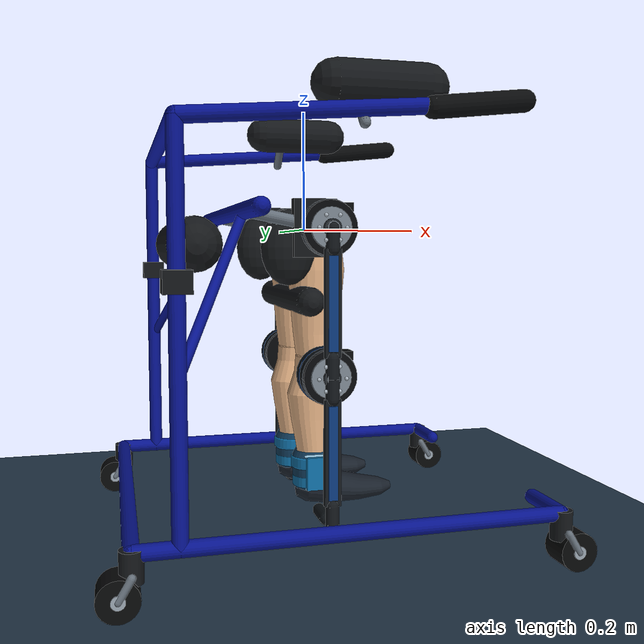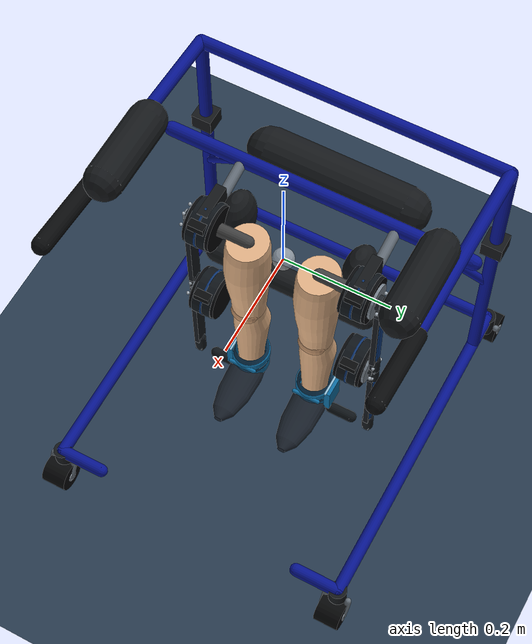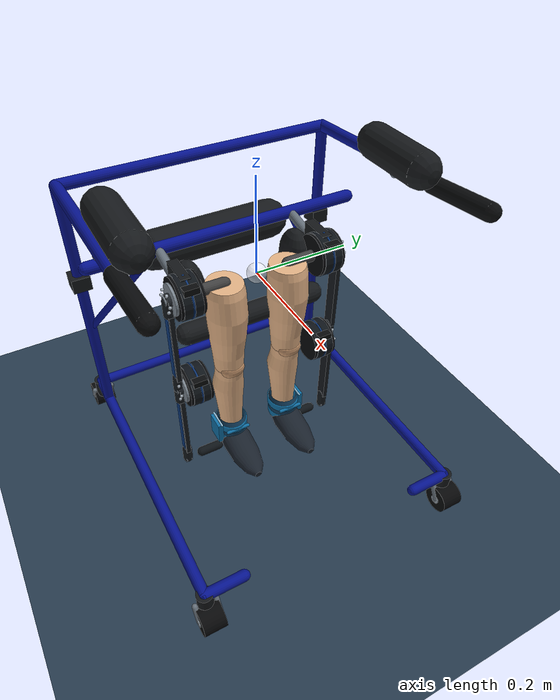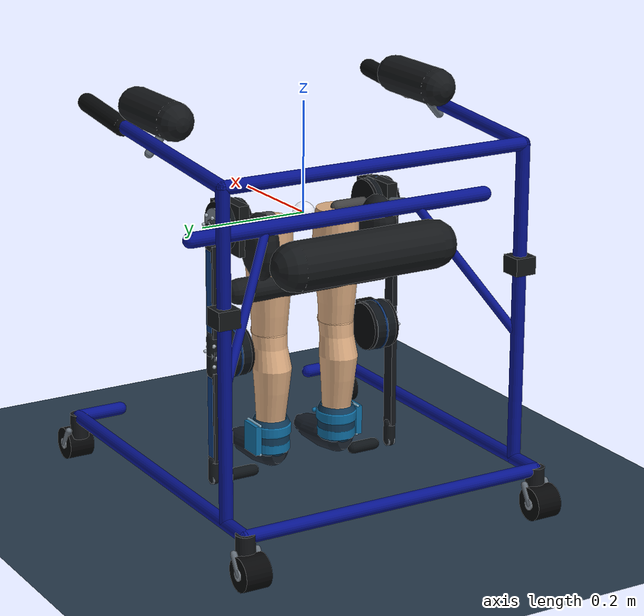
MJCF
<?xml version="1.0" encoding="utf-8"?>
<mujoco model="leg_and_arm_bilateral">
  <compiler angle="radian" autolimits="true" />
  <option timestep="0.001" gravity="0 0 -9.81" integrator="implicitfast" />
  <!-- ── 시각 설정 ─────────────────────────────────────────────── -->
  <visual>
    <global offwidth="1920" offheight="1080" />
    <headlight ambient="0.4 0.4 0.4" diffuse="0.8 0.8 0.8" specular="0.2 0.2 0.2" />
    <rgba haze="0.15 0.25 0.35 1" />
  </visual>
  <!-- ── 기본 재질/지오메트리 ──────────────────────────────────── -->
  <asset>
    <mesh name="human_thigh_mesh" vertex="0.04000 0.00000 0.00000 0.03864 0.00958 0.00000 0.03464 0.01850 0.00000 0.02828 0.02616 0.00000 0.02000 0.03204 0.00000 0.01035 0.03574 0.00000 0.00000 0.03700 0.00000 -0.01035 0.03574 0.00000 -0.02000 0.03204 0.00000 -0.02828 0.02616 0.00000 -0.03464 0.01850 0.00000 -0.03864 0.00958 0.00000 -0.04000 0.00000 0.00000 -0.03864 -0.00958 0.00000 -0.03464 -0.01850 0.00000 -0.02828 -0.02616 0.00000 -0.02000 -0.03204 0.00000 -0.01035 -0.03574 0.00000 -0.00000 -0.03700 0.00000 0.01035 -0.03574 0.00000 0.02000 -0.03204 0.00000 0.02828 -0.02616 0.00000 0.03464 -0.01850 0.00000 0.03864 -0.00958 0.00000 0.04500 0.00000 -0.01678 0.04350 0.01035 -0.01678 0.03911 0.02000 -0.01678 0.03211 0.02828 -0.01678 0.02300 0.03464 -0.01678 0.01239 0.03864 -0.01678 0.00100 0.04000 -0.01678 -0.01039 0.03864 -0.01678 -0.02100 0.03464 -0.01678 -0.03011 0.02828 -0.01678 -0.03711 0.02000 -0.01678 -0.04150 0.01035 -0.01678 -0.04300 0.00000 -0.01678 -0.04150 -0.01035 -0.01678 -0.03711 -0.02000 -0.01678 -0.03011 -0.02828 -0.01678 -0.02100 -0.03464 -0.01678 -0.01039 -0.03864 -0.01678 0.00100 -0.04000 -0.01678 0.01239 -0.03864 -0.01678 0.02300 -0.03464 -0.01678 0.03211 -0.02828 -0.01678 0.03911 -0.02000 -0.01678 0.04350 -0.01035 -0.01678 0.05100 0.00000 -0.06711 0.04940 0.01061 -0.06711 0.04470 0.02050 -0.06711 0.03723 0.02899 -0.06711 0.02750 0.03551 -0.06711 0.01616 0.03960 -0.06711 0.00400 0.04100 -0.06711 -0.00816 0.03960 -0.06711 -0.01950 0.03551 -0.06711 -0.02923 0.02899 -0.06711 -0.03670 0.02050 -0.06711 -0.04140 0.01061 -0.06711 -0.04300 0.00000 -0.06711 -0.04140 -0.01061 -0.06711 -0.03670 -0.02050 -0.06711 -0.02923 -0.02899 -0.06711 -0.01950 -0.03551 -0.06711 -0.00816 -0.03960 -0.06711 0.00400 -0.04100 -0.06711 0.01616 -0.03960 -0.06711 0.02750 -0.03551 -0.06711 0.03723 -0.02899 -0.06711 0.04470 -0.02050 -0.06711 0.04940 -0.01061 -0.06711 0.04600 0.00000 -0.12164 0.04453 0.00984 -0.12164 0.04024 0.01900 -0.12164 0.03341 0.02687 -0.12164 0.02450 0.03291 -0.12164 0.01413 0.03671 -0.12164 0.00300 0.03800 -0.12164 -0.00813 0.03671 -0.12164 -0.01850 0.03291 -0.12164 -0.02741 0.02687 -0.12164 -0.03424 0.01900 -0.12164 -0.03853 0.00984 -0.12164 -0.04000 0.00000 -0.12164 -0.03853 -0.00984 -0.12164 -0.03424 -0.01900 -0.12164 -0.02741 -0.02687 -0.12164 -0.01850 -0.03291 -0.12164 -0.00813 -0.03671 -0.12164 0.00300 -0.03800 -0.12164 0.01413 -0.03671 -0.12164 0.02450 -0.03291 -0.12164 0.03341 -0.02687 -0.12164 0.04024 -0.01900 -0.12164 0.04453 -0.00984 -0.12164 0.03700 0.00000 -0.17197 0.03577 0.00854 -0.17197 0.03218 0.01650 -0.17197 0.02646 0.02333 -0.17197 0.01900 0.02858 -0.17197 0.01032 0.03188 -0.17197 0.00100 0.03300 -0.17197 -0.00832 0.03188 -0.17197 -0.01700 0.02858 -0.17197 -0.02446 0.02333 -0.17197 -0.03018 0.01650 -0.17197 -0.03377 0.00854 -0.17197 -0.03500 0.00000 -0.17197 -0.03377 -0.00854 -0.17197 -0.03018 -0.01650 -0.17197 -0.02446 -0.02333 -0.17197 -0.01700 -0.02858 -0.17197 -0.00832 -0.03188 -0.17197 0.00100 -0.03300 -0.17197 0.01032 -0.03188 -0.17197 0.01900 -0.02858 -0.17197 0.02646 -0.02333 -0.17197 0.03218 -0.01650 -0.17197 0.03577 -0.00854 -0.17197 0.03600 0.00000 -0.20972 0.03488 0.00802 -0.20972 0.03158 0.01550 -0.20972 0.02633 0.02192 -0.20972 0.01950 0.02685 -0.20972 0.01154 0.02994 -0.20972 0.00300 0.03100 -0.20972 -0.00554 0.02994 -0.20972 -0.01350 0.02685 -0.20972 -0.02033 0.02192 -0.20972 -0.02558 0.01550 -0.20972 -0.02888 0.00802 -0.20972 -0.03000 0.00000 -0.20972 -0.02888 -0.00802 -0.20972 -0.02558 -0.01550 -0.20972 -0.02033 -0.02192 -0.20972 -0.01350 -0.02685 -0.20972 -0.00554 -0.02994 -0.20972 0.00300 -0.03100 -0.20972 0.01154 -0.02994 -0.20972 0.01950 -0.02685 -0.20972 0.02633 -0.02192 -0.20972 0.03158 -0.01550 -0.20972 0.03488 -0.00802 -0.20972 0.00000 0.00000 0.00000 0.00300 0.00000 -0.20972" face="0 24 1 1 24 25 1 25 2 2 25 26 2 26 3 3 26 27 3 27 4 4 27 28 4 28 5 5 28 29 5 29 6 6 29 30 6 30 7 7 30 31 7 31 8 8 31 32 8 32 9 9 32 33 9 33 10 10 33 34 10 34 11 11 34 35 11 35 12 12 35 36 12 36 13 13 36 37 13 37 14 14 37 38 14 38 15 15 38 39 15 39 16 16 39 40 16 40 17 17 40 41 17 41 18 18 41 42 18 42 19 19 42 43 19 43 20 20 43 44 20 44 21 21 44 45 21 45 22 22 45 46 22 46 23 23 46 47 23 47 0 0 47 24 24 48 25 25 48 49 25 49 26 26 49 50 26 50 27 27 50 51 27 51 28 28 51 52 28 52 29 29 52 53 29 53 30 30 53 54 30 54 31 31 54 55 31 55 32 32 55 56 32 56 33 33 56 57 33 57 34 34 57 58 34 58 35 35 58 59 35 59 36 36 59 60 36 60 37 37 60 61 37 61 38 38 61 62 38 62 39 39 62 63 39 63 40 40 63 64 40 64 41 41 64 65 41 65 42 42 65 66 42 66 43 43 66 67 43 67 44 44 67 68 44 68 45 45 68 69 45 69 46 46 69 70 46 70 47 47 70 71 47 71 24 24 71 48 48 72 49 49 72 73 49 73 50 50 73 74 50 74 51 51 74 75 51 75 52 52 75 76 52 76 53 53 76 77 53 77 54 54 77 78 54 78 55 55 78 79 55 79 56 56 79 80 56 80 57 57 80 81 57 81 58 58 81 82 58 82 59 59 82 83 59 83 60 60 83 84 60 84 61 61 84 85 61 85 62 62 85 86 62 86 63 63 86 87 63 87 64 64 87 88 64 88 65 65 88 89 65 89 66 66 89 90 66 90 67 67 90 91 67 91 68 68 91 92 68 92 69 69 92 93 69 93 70 70 93 94 70 94 71 71 94 95 71 95 48 48 95 72 72 96 73 73 96 97 73 97 74 74 97 98 74 98 75 75 98 99 75 99 76 76 99 100 76 100 77 77 100 101 77 101 78 78 101 102 78 102 79 79 102 103 79 103 80 80 103 104 80 104 81 81 104 105 81 105 82 82 105 106 82 106 83 83 106 107 83 107 84 84 107 108 84 108 85 85 108 109 85 109 86 86 109 110 86 110 87 87 110 111 87 111 88 88 111 112 88 112 89 89 112 113 89 113 90 90 113 114 90 114 91 91 114 115 91 115 92 92 115 116 92 116 93 93 116 117 93 117 94 94 117 118 94 118 95 95 118 119 95 119 72 72 119 96 96 120 97 97 120 121 97 121 98 98 121 122 98 122 99 99 122 123 99 123 100 100 123 124 100 124 101 101 124 125 101 125 102 102 125 126 102 126 103 103 126 127 103 127 104 104 127 128 104 128 105 105 128 129 105 129 106 106 129 130 106 130 107 107 130 131 107 131 108 108 131 132 108 132 109 109 132 133 109 133 110 110 133 134 110 134 111 111 134 135 111 135 112 112 135 136 112 136 113 113 136 137 113 137 114 114 137 138 114 138 115 115 138 139 115 139 116 116 139 140 116 140 117 117 140 141 117 141 118 118 141 142 118 142 119 119 142 143 119 143 96 96 143 120 144 1 0 145 120 121 144 2 1 145 121 122 144 3 2 145 122 123 144 4 3 145 123 124 144 5 4 145 124 125 144 6 5 145 125 126 144 7 6 145 126 127 144 8 7 145 127 128 144 9 8 145 128 129 144 10 9 145 129 130 144 11 10 145 130 131 144 12 11 145 131 132 144 13 12 145 132 133 144 14 13 145 133 134 144 15 14 145 134 135 144 16 15 145 135 136 144 17 16 145 136 137 144 18 17 145 137 138 144 19 18 145 138 139 144 20 19 145 139 140 144 21 20 145 140 141 144 22 21 145 141 142 144 23 22 145 142 143 144 0 23 145 143 120" />
    <mesh name="human_shank_mesh" vertex="0.03700 0.00000 0.00000 0.03584 0.00802 0.00000 0.03244 0.01550 0.00000 0.02704 0.02192 0.00000 0.02000 0.02685 0.00000 0.01180 0.02994 0.00000 0.00300 0.03100 0.00000 -0.00580 0.02994 0.00000 -0.01400 0.02685 0.00000 -0.02104 0.02192 0.00000 -0.02644 0.01550 0.00000 -0.02984 0.00802 0.00000 -0.03100 0.00000 0.00000 -0.02984 -0.00802 0.00000 -0.02644 -0.01550 0.00000 -0.02104 -0.02192 0.00000 -0.01400 -0.02685 0.00000 -0.00580 -0.02994 0.00000 0.00300 -0.03100 0.00000 0.01180 -0.02994 0.00000 0.02000 -0.02685 0.00000 0.02704 -0.02192 0.00000 0.03244 -0.01550 0.00000 0.03584 -0.00802 0.00000 0.03300 0.00000 -0.02527 0.03188 0.00776 -0.02527 0.02858 0.01500 -0.02527 0.02333 0.02121 -0.02527 0.01650 0.02598 -0.02527 0.00854 0.02898 -0.02527 0.00000 0.03000 -0.02527 -0.00854 0.02898 -0.02527 -0.01650 0.02598 -0.02527 -0.02333 0.02121 -0.02527 -0.02858 0.01500 -0.02527 -0.03188 0.00776 -0.02527 -0.03300 0.00000 -0.02527 -0.03188 -0.00776 -0.02527 -0.02858 -0.01500 -0.02527 -0.02333 -0.02121 -0.02527 -0.01650 -0.02598 -0.02527 -0.00854 -0.02898 -0.02527 -0.00000 -0.03000 -0.02527 0.00854 -0.02898 -0.02527 0.01650 -0.02598 -0.02527 0.02333 -0.02121 -0.02527 0.02858 -0.01500 -0.02527 0.03188 -0.00776 -0.02527 0.03100 0.00000 -0.06317 0.02971 0.00880 -0.06317 0.02591 0.01700 -0.06317 0.01987 0.02404 -0.06317 0.01200 0.02944 -0.06317 0.00284 0.03284 -0.06317 -0.00700 0.03400 -0.06317 -0.01684 0.03284 -0.06317 -0.02600 0.02944 -0.06317 -0.03387 0.02404 -0.06317 -0.03991 0.01700 -0.06317 -0.04371 0.00880 -0.06317 -0.04500 0.00000 -0.06317 -0.04371 -0.00880 -0.06317 -0.03991 -0.01700 -0.06317 -0.03387 -0.02404 -0.06317 -0.02600 -0.02944 -0.06317 -0.01684 -0.03284 -0.06317 -0.00700 -0.03400 -0.06317 0.00284 -0.03284 -0.06317 0.01200 -0.02944 -0.06317 0.01987 -0.02404 -0.06317 0.02591 -0.01700 -0.06317 0.02971 -0.00880 -0.06317 0.02900 0.00000 -0.10529 0.02784 0.00776 -0.10529 0.02444 0.01500 -0.10529 0.01904 0.02121 -0.10529 0.01200 0.02598 -0.10529 0.00380 0.02898 -0.10529 -0.00500 0.03000 -0.10529 -0.01380 0.02898 -0.10529 -0.02200 0.02598 -0.10529 -0.02904 0.02121 -0.10529 -0.03444 0.01500 -0.10529 -0.03784 0.00776 -0.10529 -0.03900 0.00000 -0.10529 -0.03784 -0.00776 -0.10529 -0.03444 -0.01500 -0.10529 -0.02904 -0.02121 -0.10529 -0.02200 -0.02598 -0.10529 -0.01380 -0.02898 -0.10529 -0.00500 -0.03000 -0.10529 0.00380 -0.02898 -0.10529 0.01200 -0.02598 -0.10529 0.01904 -0.02121 -0.10529 0.02444 -0.01500 -0.10529 0.02784 -0.00776 -0.10529 0.02700 0.00000 -0.15793 0.02605 0.00673 -0.15793 0.02325 0.01300 -0.15793 0.01880 0.01838 -0.15793 0.01300 0.02252 -0.15793 0.00625 0.02511 -0.15793 -0.00100 0.02600 -0.15793 -0.00825 0.02511 -0.15793 -0.01500 0.02252 -0.15793 -0.02080 0.01838 -0.15793 -0.02525 0.01300 -0.15793 -0.02805 0.00673 -0.15793 -0.02900 0.00000 -0.15793 -0.02805 -0.00673 -0.15793 -0.02525 -0.01300 -0.15793 -0.02080 -0.01838 -0.15793 -0.01500 -0.02252 -0.15793 -0.00825 -0.02511 -0.15793 -0.00100 -0.02600 -0.15793 0.00625 -0.02511 -0.15793 0.01300 -0.02252 -0.15793 0.01880 -0.01838 -0.15793 0.02325 -0.01300 -0.15793 0.02605 -0.00673 -0.15793 0.02400 0.00000 -0.21058 0.02318 0.00595 -0.21058 0.02078 0.01150 -0.21058 0.01697 0.01626 -0.21058 0.01200 0.01992 -0.21058 0.00621 0.02222 -0.21058 0.00000 0.02300 -0.21058 -0.00621 0.02222 -0.21058 -0.01200 0.01992 -0.21058 -0.01697 0.01626 -0.21058 -0.02078 0.01150 -0.21058 -0.02318 0.00595 -0.21058 -0.02400 0.00000 -0.21058 -0.02318 -0.00595 -0.21058 -0.02078 -0.01150 -0.21058 -0.01697 -0.01626 -0.21058 -0.01200 -0.01992 -0.21058 -0.00621 -0.02222 -0.21058 -0.00000 -0.02300 -0.21058 0.00621 -0.02222 -0.21058 0.01200 -0.01992 -0.21058 0.01697 -0.01626 -0.21058 0.02078 -0.01150 -0.21058 0.02318 -0.00595 -0.21058 0.00300 0.00000 0.00000 0.00000 0.00000 -0.21058" face="0 24 1 1 24 25 1 25 2 2 25 26 2 26 3 3 26 27 3 27 4 4 27 28 4 28 5 5 28 29 5 29 6 6 29 30 6 30 7 7 30 31 7 31 8 8 31 32 8 32 9 9 32 33 9 33 10 10 33 34 10 34 11 11 34 35 11 35 12 12 35 36 12 36 13 13 36 37 13 37 14 14 37 38 14 38 15 15 38 39 15 39 16 16 39 40 16 40 17 17 40 41 17 41 18 18 41 42 18 42 19 19 42 43 19 43 20 20 43 44 20 44 21 21 44 45 21 45 22 22 45 46 22 46 23 23 46 47 23 47 0 0 47 24 24 48 25 25 48 49 25 49 26 26 49 50 26 50 27 27 50 51 27 51 28 28 51 52 28 52 29 29 52 53 29 53 30 30 53 54 30 54 31 31 54 55 31 55 32 32 55 56 32 56 33 33 56 57 33 57 34 34 57 58 34 58 35 35 58 59 35 59 36 36 59 60 36 60 37 37 60 61 37 61 38 38 61 62 38 62 39 39 62 63 39 63 40 40 63 64 40 64 41 41 64 65 41 65 42 42 65 66 42 66 43 43 66 67 43 67 44 44 67 68 44 68 45 45 68 69 45 69 46 46 69 70 46 70 47 47 70 71 47 71 24 24 71 48 48 72 49 49 72 73 49 73 50 50 73 74 50 74 51 51 74 75 51 75 52 52 75 76 52 76 53 53 76 77 53 77 54 54 77 78 54 78 55 55 78 79 55 79 56 56 79 80 56 80 57 57 80 81 57 81 58 58 81 82 58 82 59 59 82 83 59 83 60 60 83 84 60 84 61 61 84 85 61 85 62 62 85 86 62 86 63 63 86 87 63 87 64 64 87 88 64 88 65 65 88 89 65 89 66 66 89 90 66 90 67 67 90 91 67 91 68 68 91 92 68 92 69 69 92 93 69 93 70 70 93 94 70 94 71 71 94 95 71 95 48 48 95 72 72 96 73 73 96 97 73 97 74 74 97 98 74 98 75 75 98 99 75 99 76 76 99 100 76 100 77 77 100 101 77 101 78 78 101 102 78 102 79 79 102 103 79 103 80 80 103 104 80 104 81 81 104 105 81 105 82 82 105 106 82 106 83 83 106 107 83 107 84 84 107 108 84 108 85 85 108 109 85 109 86 86 109 110 86 110 87 87 110 111 87 111 88 88 111 112 88 112 89 89 112 113 89 113 90 90 113 114 90 114 91 91 114 115 91 115 92 92 115 116 92 116 93 93 116 117 93 117 94 94 117 118 94 118 95 95 118 119 95 119 72 72 119 96 96 120 97 97 120 121 97 121 98 98 121 122 98 122 99 99 122 123 99 123 100 100 123 124 100 124 101 101 124 125 101 125 102 102 125 126 102 126 103 103 126 127 103 127 104 104 127 128 104 128 105 105 128 129 105 129 106 106 129 130 106 130 107 107 130 131 107 131 108 108 131 132 108 132 109 109 132 133 109 133 110 110 133 134 110 134 111 111 134 135 111 135 112 112 135 136 112 136 113 113 136 137 113 137 114 114 137 138 114 138 115 115 138 139 115 139 116 116 139 140 116 140 117 117 140 141 117 141 118 118 141 142 118 142 119 119 142 143 119 143 96 96 143 120 144 1 0 145 120 121 144 2 1 145 121 122 144 3 2 145 122 123 144 4 3 145 123 124 144 5 4 145 124 125 144 6 5 145 125 126 144 7 6 145 126 127 144 8 7 145 127 128 144 9 8 145 128 129 144 10 9 145 129 130 144 11 10 145 130 131 144 12 11 145 131 132 144 13 12 145 132 133 144 14 13 145 133 134 144 15 14 145 134 135 144 16 15 145 135 136 144 17 16 145 136 137 144 18 17 145 137 138 144 19 18 145 138 139 144 20 19 145 139 140 144 21 20 145 140 141 144 22 21 145 141 142 144 23 22 145 142 143 144 0 23 145 143 120" />
    <mesh name="human_foot_mesh" vertex="-0.03000 0.00000 0.00800 -0.03000 0.00362 0.00739 -0.03000 0.00700 0.00559 -0.03000 0.00990 0.00273 -0.03000 0.01212 -0.00100 -0.03000 0.01352 -0.00534 -0.03000 0.01400 -0.01000 -0.03000 0.01352 -0.01466 -0.03000 0.01212 -0.01900 -0.03000 0.00990 -0.02273 -0.03000 0.00700 -0.02559 -0.03000 0.00362 -0.02739 -0.03000 0.00000 -0.02800 -0.03000 -0.00362 -0.02739 -0.03000 -0.00700 -0.02559 -0.03000 -0.00990 -0.02273 -0.03000 -0.01212 -0.01900 -0.03000 -0.01352 -0.01466 -0.03000 -0.01400 -0.01000 -0.03000 -0.01352 -0.00534 -0.03000 -0.01212 -0.00100 -0.03000 -0.00990 0.00273 -0.03000 -0.00700 0.00559 -0.03000 -0.00362 0.00739 -0.01500 0.00000 0.01700 -0.01500 0.00725 0.01608 -0.01500 0.01400 0.01338 -0.01500 0.01980 0.00909 -0.01500 0.02425 0.00350 -0.01500 0.02705 -0.00301 -0.01500 0.02800 -0.01000 -0.01500 0.02705 -0.01699 -0.01500 0.02425 -0.02350 -0.01500 0.01980 -0.02909 -0.01500 0.01400 -0.03338 -0.01500 0.00725 -0.03608 -0.01500 0.00000 -0.03700 -0.01500 -0.00725 -0.03608 -0.01500 -0.01400 -0.03338 -0.01500 -0.01980 -0.02909 -0.01500 -0.02425 -0.02350 -0.01500 -0.02705 -0.01699 -0.01500 -0.02800 -0.01000 -0.01500 -0.02705 -0.00301 -0.01500 -0.02425 0.00350 -0.01500 -0.01980 0.00909 -0.01500 -0.01400 0.01338 -0.01500 -0.00725 0.01608 0.02500 0.00000 0.01400 0.02500 0.00906 0.01305 0.02500 0.01750 0.01025 0.02500 0.02475 0.00580 0.02500 0.03031 0.00000 0.02500 0.03381 -0.00675 0.02500 0.03500 -0.01400 0.02500 0.03381 -0.02125 0.02500 0.03031 -0.02800 0.02500 0.02475 -0.03380 0.02500 0.01750 -0.03825 0.02500 0.00906 -0.04105 0.02500 0.00000 -0.04200 0.02500 -0.00906 -0.04105 0.02500 -0.01750 -0.03825 0.02500 -0.02475 -0.03380 0.02500 -0.03031 -0.02800 0.02500 -0.03381 -0.02125 0.02500 -0.03500 -0.01400 0.02500 -0.03381 -0.00675 0.02500 -0.03031 0.00000 0.02500 -0.02475 0.00580 0.02500 -0.01750 0.01025 0.02500 -0.00906 0.01305 0.07500 0.00000 0.00200 0.07500 0.00854 0.00128 0.07500 0.01650 -0.00081 0.07500 0.02333 -0.00415 0.07500 0.02858 -0.00850 0.07500 0.03188 -0.01356 0.07500 0.03300 -0.01900 0.07500 0.03188 -0.02444 0.07500 0.02858 -0.02950 0.07500 0.02333 -0.03385 0.07500 0.01650 -0.03719 0.07500 0.00854 -0.03928 0.07500 0.00000 -0.04000 0.07500 -0.00854 -0.03928 0.07500 -0.01650 -0.03719 0.07500 -0.02333 -0.03385 0.07500 -0.02858 -0.02950 0.07500 -0.03188 -0.02444 0.07500 -0.03300 -0.01900 0.07500 -0.03188 -0.01356 0.07500 -0.02858 -0.00850 0.07500 -0.02333 -0.00415 0.07500 -0.01650 -0.00081 0.07500 -0.00854 0.00128 0.11500 0.00000 -0.00600 0.11500 0.00595 -0.00651 0.11500 0.01150 -0.00801 0.11500 0.01626 -0.01039 0.11500 0.01992 -0.01350 0.11500 0.02222 -0.01712 0.11500 0.02300 -0.02100 0.11500 0.02222 -0.02488 0.11500 0.01992 -0.02850 0.11500 0.01626 -0.03161 0.11500 0.01150 -0.03399 0.11500 0.00595 -0.03549 0.11500 0.00000 -0.03600 0.11500 -0.00595 -0.03549 0.11500 -0.01150 -0.03399 0.11500 -0.01626 -0.03161 0.11500 -0.01992 -0.02850 0.11500 -0.02222 -0.02488 0.11500 -0.02300 -0.02100 0.11500 -0.02222 -0.01712 0.11500 -0.01992 -0.01350 0.11500 -0.01626 -0.01039 0.11500 -0.01150 -0.00801 0.11500 -0.00595 -0.00651 0.13500 0.00000 -0.01400 0.13500 0.00207 -0.01424 0.13500 0.00400 -0.01494 0.13500 0.00566 -0.01605 0.13500 0.00693 -0.01750 0.13500 0.00773 -0.01919 0.13500 0.00800 -0.02100 0.13500 0.00773 -0.02281 0.13500 0.00693 -0.02450 0.13500 0.00566 -0.02595 0.13500 0.00400 -0.02706 0.13500 0.00207 -0.02776 0.13500 0.00000 -0.02800 0.13500 -0.00207 -0.02776 0.13500 -0.00400 -0.02706 0.13500 -0.00566 -0.02595 0.13500 -0.00693 -0.02450 0.13500 -0.00773 -0.02281 0.13500 -0.00800 -0.02100 0.13500 -0.00773 -0.01919 0.13500 -0.00693 -0.01750 0.13500 -0.00566 -0.01605 0.13500 -0.00400 -0.01494 0.13500 -0.00207 -0.01424 -0.03000 0.00000 -0.01000 0.13500 0.00000 -0.02100" face="0 1 24 1 25 24 1 2 25 2 26 25 2 3 26 3 27 26 3 4 27 4 28 27 4 5 28 5 29 28 5 6 29 6 30 29 6 7 30 7 31 30 7 8 31 8 32 31 8 9 32 9 33 32 9 10 33 10 34 33 10 11 34 11 35 34 11 12 35 12 36 35 12 13 36 13 37 36 13 14 37 14 38 37 14 15 38 15 39 38 15 16 39 16 40 39 16 17 40 17 41 40 17 18 41 18 42 41 18 19 42 19 43 42 19 20 43 20 44 43 20 21 44 21 45 44 21 22 45 22 46 45 22 23 46 23 47 46 23 0 47 0 24 47 24 25 48 25 49 48 25 26 49 26 50 49 26 27 50 27 51 50 27 28 51 28 52 51 28 29 52 29 53 52 29 30 53 30 54 53 30 31 54 31 55 54 31 32 55 32 56 55 32 33 56 33 57 56 33 34 57 34 58 57 34 35 58 35 59 58 35 36 59 36 60 59 36 37 60 37 61 60 37 38 61 38 62 61 38 39 62 39 63 62 39 40 63 40 64 63 40 41 64 41 65 64 41 42 65 42 66 65 42 43 66 43 67 66 43 44 67 44 68 67 44 45 68 45 69 68 45 46 69 46 70 69 46 47 70 47 71 70 47 24 71 24 48 71 48 49 72 49 73 72 49 50 73 50 74 73 50 51 74 51 75 74 51 52 75 52 76 75 52 53 76 53 77 76 53 54 77 54 78 77 54 55 78 55 79 78 55 56 79 56 80 79 56 57 80 57 81 80 57 58 81 58 82 81 58 59 82 59 83 82 59 60 83 60 84 83 60 61 84 61 85 84 61 62 85 62 86 85 62 63 86 63 87 86 63 64 87 64 88 87 64 65 88 65 89 88 65 66 89 66 90 89 66 67 90 67 91 90 67 68 91 68 92 91 68 69 92 69 93 92 69 70 93 70 94 93 70 71 94 71 95 94 71 48 95 48 72 95 72 73 96 73 97 96 73 74 97 74 98 97 74 75 98 75 99 98 75 76 99 76 100 99 76 77 100 77 101 100 77 78 101 78 102 101 78 79 102 79 103 102 79 80 103 80 104 103 80 81 104 81 105 104 81 82 105 82 106 105 82 83 106 83 107 106 83 84 107 84 108 107 84 85 108 85 109 108 85 86 109 86 110 109 86 87 110 87 111 110 87 88 111 88 112 111 88 89 112 89 113 112 89 90 113 90 114 113 90 91 114 91 115 114 91 92 115 92 116 115 92 93 116 93 117 116 93 94 117 94 118 117 94 95 118 95 119 118 95 72 119 72 96 119 96 97 120 97 121 120 97 98 121 98 122 121 98 99 122 99 123 122 99 100 123 100 124 123 100 101 124 101 125 124 101 102 125 102 126 125 102 103 126 103 127 126 103 104 127 104 128 127 104 105 128 105 129 128 105 106 129 106 130 129 106 107 130 107 131 130 107 108 131 108 132 131 108 109 132 109 133 132 109 110 133 110 134 133 110 111 134 111 135 134 111 112 135 112 136 135 112 113 136 113 137 136 113 114 137 114 138 137 114 115 138 115 139 138 115 116 139 116 140 139 116 117 140 117 141 140 117 118 141 118 142 141 118 119 142 119 143 142 119 96 143 96 120 143 144 0 1 145 121 120 144 1 2 145 122 121 144 2 3 145 123 122 144 3 4 145 124 123 144 4 5 145 125 124 144 5 6 145 126 125 144 6 7 145 127 126 144 7 8 145 128 127 144 8 9 145 129 128 144 9 10 145 130 129 144 10 11 145 131 130 144 11 12 145 132 131 144 12 13 145 133 132 144 13 14 145 134 133 144 14 15 145 135 134 144 15 16 145 136 135 144 16 17 145 137 136 144 17 18 145 138 137 144 18 19 145 139 138 144 19 20 145 140 139 144 20 21 145 141 140 144 21 22 145 142 141 144 22 23 145 143 142 144 23 0 145 120 143" />
    <mesh name="ankle_soft_cuff_mesh" vertex="0.03000 0.00000 -0.01400 0.02942 0.00546 -0.01400 0.02772 0.01072 -0.01400 0.02494 0.01556 -0.01400 0.02121 0.01980 -0.01400 0.01667 0.02328 -0.01400 0.01148 0.02587 -0.01400 0.00585 0.02746 -0.01400 0.00000 0.02800 -0.01400 -0.00585 0.02746 -0.01400 -0.01148 0.02587 -0.01400 -0.01667 0.02328 -0.01400 -0.02121 0.01980 -0.01400 -0.02494 0.01556 -0.01400 -0.02772 0.01072 -0.01400 -0.02942 0.00546 -0.01400 -0.03000 0.00000 -0.01400 -0.02942 -0.00546 -0.01400 -0.02772 -0.01072 -0.01400 -0.02494 -0.01556 -0.01400 -0.02121 -0.01980 -0.01400 -0.01667 -0.02328 -0.01400 -0.01148 -0.02587 -0.01400 -0.00585 -0.02746 -0.01400 -0.00000 -0.02800 -0.01400 0.00585 -0.02746 -0.01400 0.01148 -0.02587 -0.01400 0.01667 -0.02328 -0.01400 0.02121 -0.01980 -0.01400 0.02494 -0.01556 -0.01400 0.02772 -0.01072 -0.01400 0.02942 -0.00546 -0.01400 0.03500 0.00000 -0.00800 0.03433 0.00644 -0.00800 0.03234 0.01263 -0.00800 0.02910 0.01833 -0.00800 0.02475 0.02333 -0.00800 0.01944 0.02744 -0.00800 0.01339 0.03049 -0.00800 0.00683 0.03237 -0.00800 0.00000 0.03300 -0.00800 -0.00683 0.03237 -0.00800 -0.01339 0.03049 -0.00800 -0.01944 0.02744 -0.00800 -0.02475 0.02333 -0.00800 -0.02910 0.01833 -0.00800 -0.03234 0.01263 -0.00800 -0.03433 0.00644 -0.00800 -0.03500 0.00000 -0.00800 -0.03433 -0.00644 -0.00800 -0.03234 -0.01263 -0.00800 -0.02910 -0.01833 -0.00800 -0.02475 -0.02333 -0.00800 -0.01944 -0.02744 -0.00800 -0.01339 -0.03049 -0.00800 -0.00683 -0.03237 -0.00800 -0.00000 -0.03300 -0.00800 0.00683 -0.03237 -0.00800 0.01339 -0.03049 -0.00800 0.01944 -0.02744 -0.00800 0.02475 -0.02333 -0.00800 0.02910 -0.01833 -0.00800 0.03234 -0.01263 -0.00800 0.03433 -0.00644 -0.00800 0.03700 0.00000 0.04200 0.03629 0.00663 0.04200 0.03418 0.01301 0.04200 0.03076 0.01889 0.04200 0.02616 0.02404 0.04200 0.02056 0.02827 0.04200 0.01416 0.03141 0.04200 0.00722 0.03335 0.04200 0.00000 0.03400 0.04200 -0.00722 0.03335 0.04200 -0.01416 0.03141 0.04200 -0.02056 0.02827 0.04200 -0.02616 0.02404 0.04200 -0.03076 0.01889 0.04200 -0.03418 0.01301 0.04200 -0.03629 0.00663 0.04200 -0.03700 0.00000 0.04200 -0.03629 -0.00663 0.04200 -0.03418 -0.01301 0.04200 -0.03076 -0.01889 0.04200 -0.02616 -0.02404 0.04200 -0.02056 -0.02827 0.04200 -0.01416 -0.03141 0.04200 -0.00722 -0.03335 0.04200 -0.00000 -0.03400 0.04200 0.00722 -0.03335 0.04200 0.01416 -0.03141 0.04200 0.02056 -0.02827 0.04200 0.02616 -0.02404 0.04200 0.03076 -0.01889 0.04200 0.03418 -0.01301 0.04200 0.03629 -0.00663 0.04200 0.03200 0.00000 0.05200 0.03139 0.00585 0.05200 0.02956 0.01148 0.05200 0.02661 0.01667 0.05200 0.02263 0.02121 0.05200 0.01778 0.02494 0.05200 0.01225 0.02772 0.05200 0.00624 0.02942 0.05200 0.00000 0.03000 0.05200 -0.00624 0.02942 0.05200 -0.01225 0.02772 0.05200 -0.01778 0.02494 0.05200 -0.02263 0.02121 0.05200 -0.02661 0.01667 0.05200 -0.02956 0.01148 0.05200 -0.03139 0.00585 0.05200 -0.03200 0.00000 0.05200 -0.03139 -0.00585 0.05200 -0.02956 -0.01148 0.05200 -0.02661 -0.01667 0.05200 -0.02263 -0.02121 0.05200 -0.01778 -0.02494 0.05200 -0.01225 -0.02772 0.05200 -0.00624 -0.02942 0.05200 -0.00000 -0.03000 0.05200 0.00624 -0.02942 0.05200 0.01225 -0.02772 0.05200 0.01778 -0.02494 0.05200 0.02263 -0.02121 0.05200 0.02661 -0.01667 0.05200 0.02956 -0.01148 0.05200 0.03139 -0.00585 0.05200" face="0 32 1 1 32 33 1 33 2 2 33 34 2 34 3 3 34 35 3 35 4 4 35 36 4 36 5 5 36 37 5 37 6 6 37 38 6 38 7 7 38 39 7 39 8 8 39 40 8 40 9 9 40 41 9 41 10 10 41 42 10 42 11 11 42 43 11 43 12 12 43 44 12 44 13 13 44 45 13 45 14 14 45 46 14 46 15 15 46 47 15 47 16 16 47 48 16 48 17 17 48 49 17 49 18 18 49 50 18 50 19 19 50 51 19 51 20 20 51 52 20 52 21 21 52 53 21 53 22 22 53 54 22 54 23 23 54 55 23 55 24 24 55 56 24 56 25 25 56 57 25 57 26 26 57 58 26 58 27 27 58 59 27 59 28 28 59 60 28 60 29 29 60 61 29 61 30 30 61 62 30 62 31 31 62 63 31 63 0 0 63 32 32 64 33 33 64 65 33 65 34 34 65 66 34 66 35 35 66 67 35 67 36 36 67 68 36 68 37 37 68 69 37 69 38 38 69 70 38 70 39 39 70 71 39 71 40 40 71 72 40 72 41 41 72 73 41 73 42 42 73 74 42 74 43 43 74 75 43 75 44 44 75 76 44 76 45 45 76 77 45 77 46 46 77 78 46 78 47 47 78 79 47 79 48 48 79 80 48 80 49 49 80 81 49 81 50 50 81 82 50 82 51 51 82 83 51 83 52 52 83 84 52 84 53 53 84 85 53 85 54 54 85 86 54 86 55 55 86 87 55 87 56 56 87 88 56 88 57 57 88 89 57 89 58 58 89 90 58 90 59 59 90 91 59 91 60 60 91 92 60 92 61 61 92 93 61 93 62 62 93 94 62 94 63 63 94 95 63 95 32 32 95 64 64 96 65 65 96 97 65 97 66 66 97 98 66 98 67 67 98 99 67 99 68 68 99 100 68 100 69 69 100 101 69 101 70 70 101 102 70 102 71 71 102 103 71 103 72 72 103 104 72 104 73 73 104 105 73 105 74 74 105 106 74 106 75 75 106 107 75 107 76 76 107 108 76 108 77 77 108 109 77 109 78 78 109 110 78 110 79 79 110 111 79 111 80 80 111 112 80 112 81 81 112 113 81 113 82 82 113 114 82 114 83 83 114 115 83 115 84 84 115 116 84 116 85 85 116 117 85 117 86 86 117 118 86 118 87 87 118 119 87 119 88 88 119 120 88 120 89 89 120 121 89 121 90 90 121 122 90 122 91 91 122 123 91 123 92 92 123 124 92 124 93 93 124 125 93 125 94 94 125 126 94 126 95 95 126 127 95 127 64 64 127 96" />
    <mesh name="ankle_soft_strap_mesh" vertex="0.03600 0.00000 0.02200 0.03531 0.00644 0.02200 0.03326 0.01263 0.02200 0.02993 0.01833 0.02200 0.02546 0.02333 0.02200 0.02000 0.02744 0.02200 0.01378 0.03049 0.02200 0.00702 0.03237 0.02200 0.00000 0.03300 0.02200 -0.00702 0.03237 0.02200 -0.01378 0.03049 0.02200 -0.02000 0.02744 0.02200 -0.02546 0.02333 0.02200 -0.02993 0.01833 0.02200 -0.03326 0.01263 0.02200 -0.03531 0.00644 0.02200 -0.03600 0.00000 0.02200 -0.03531 -0.00644 0.02200 -0.03326 -0.01263 0.02200 -0.02993 -0.01833 0.02200 -0.02546 -0.02333 0.02200 -0.02000 -0.02744 0.02200 -0.01378 -0.03049 0.02200 -0.00702 -0.03237 0.02200 -0.00000 -0.03300 0.02200 0.00702 -0.03237 0.02200 0.01378 -0.03049 0.02200 0.02000 -0.02744 0.02200 0.02546 -0.02333 0.02200 0.02993 -0.01833 0.02200 0.03326 -0.01263 0.02200 0.03531 -0.00644 0.02200 0.03900 0.00000 0.02500 0.03825 0.00702 0.02500 0.03603 0.01378 0.02500 0.03243 0.02000 0.02500 0.02758 0.02546 0.02500 0.02167 0.02993 0.02500 0.01492 0.03326 0.02500 0.00761 0.03531 0.02500 0.00000 0.03600 0.02500 -0.00761 0.03531 0.02500 -0.01492 0.03326 0.02500 -0.02167 0.02993 0.02500 -0.02758 0.02546 0.02500 -0.03243 0.02000 0.02500 -0.03603 0.01378 0.02500 -0.03825 0.00702 0.02500 -0.03900 0.00000 0.02500 -0.03825 -0.00702 0.02500 -0.03603 -0.01378 0.02500 -0.03243 -0.02000 0.02500 -0.02758 -0.02546 0.02500 -0.02167 -0.02993 0.02500 -0.01492 -0.03326 0.02500 -0.00761 -0.03531 0.02500 -0.00000 -0.03600 0.02500 0.00761 -0.03531 0.02500 0.01492 -0.03326 0.02500 0.02167 -0.02993 0.02500 0.02758 -0.02546 0.02500 0.03243 -0.02000 0.02500 0.03603 -0.01378 0.02500 0.03825 -0.00702 0.02500 0.03900 0.00000 0.04000 0.03825 0.00702 0.04000 0.03603 0.01378 0.04000 0.03243 0.02000 0.04000 0.02758 0.02546 0.04000 0.02167 0.02993 0.04000 0.01492 0.03326 0.04000 0.00761 0.03531 0.04000 0.00000 0.03600 0.04000 -0.00761 0.03531 0.04000 -0.01492 0.03326 0.04000 -0.02167 0.02993 0.04000 -0.02758 0.02546 0.04000 -0.03243 0.02000 0.04000 -0.03603 0.01378 0.04000 -0.03825 0.00702 0.04000 -0.03900 0.00000 0.04000 -0.03825 -0.00702 0.04000 -0.03603 -0.01378 0.04000 -0.03243 -0.02000 0.04000 -0.02758 -0.02546 0.04000 -0.02167 -0.02993 0.04000 -0.01492 -0.03326 0.04000 -0.00761 -0.03531 0.04000 -0.00000 -0.03600 0.04000 0.00761 -0.03531 0.04000 0.01492 -0.03326 0.04000 0.02167 -0.02993 0.04000 0.02758 -0.02546 0.04000 0.03243 -0.02000 0.04000 0.03603 -0.01378 0.04000 0.03825 -0.00702 0.04000 0.03600 0.00000 0.04300 0.03531 0.00644 0.04300 0.03326 0.01263 0.04300 0.02993 0.01833 0.04300 0.02546 0.02333 0.04300 0.02000 0.02744 0.04300 0.01378 0.03049 0.04300 0.00702 0.03237 0.04300 0.00000 0.03300 0.04300 -0.00702 0.03237 0.04300 -0.01378 0.03049 0.04300 -0.02000 0.02744 0.04300 -0.02546 0.02333 0.04300 -0.02993 0.01833 0.04300 -0.03326 0.01263 0.04300 -0.03531 0.00644 0.04300 -0.03600 0.00000 0.04300 -0.03531 -0.00644 0.04300 -0.03326 -0.01263 0.04300 -0.02993 -0.01833 0.04300 -0.02546 -0.02333 0.04300 -0.02000 -0.02744 0.04300 -0.01378 -0.03049 0.04300 -0.00702 -0.03237 0.04300 -0.00000 -0.03300 0.04300 0.00702 -0.03237 0.04300 0.01378 -0.03049 0.04300 0.02000 -0.02744 0.04300 0.02546 -0.02333 0.04300 0.02993 -0.01833 0.04300 0.03326 -0.01263 0.04300 0.03531 -0.00644 0.04300" face="0 32 1 1 32 33 1 33 2 2 33 34 2 34 3 3 34 35 3 35 4 4 35 36 4 36 5 5 36 37 5 37 6 6 37 38 6 38 7 7 38 39 7 39 8 8 39 40 8 40 9 9 40 41 9 41 10 10 41 42 10 42 11 11 42 43 11 43 12 12 43 44 12 44 13 13 44 45 13 45 14 14 45 46 14 46 15 15 46 47 15 47 16 16 47 48 16 48 17 17 48 49 17 49 18 18 49 50 18 50 19 19 50 51 19 51 20 20 51 52 20 52 21 21 52 53 21 53 22 22 53 54 22 54 23 23 54 55 23 55 24 24 55 56 24 56 25 25 56 57 25 57 26 26 57 58 26 58 27 27 58 59 27 59 28 28 59 60 28 60 29 29 60 61 29 61 30 30 61 62 30 62 31 31 62 63 31 63 0 0 63 32 32 64 33 33 64 65 33 65 34 34 65 66 34 66 35 35 66 67 35 67 36 36 67 68 36 68 37 37 68 69 37 69 38 38 69 70 38 70 39 39 70 71 39 71 40 40 71 72 40 72 41 41 72 73 41 73 42 42 73 74 42 74 43 43 74 75 43 75 44 44 75 76 44 76 45 45 76 77 45 77 46 46 77 78 46 78 47 47 78 79 47 79 48 48 79 80 48 80 49 49 80 81 49 81 50 50 81 82 50 82 51 51 82 83 51 83 52 52 83 84 52 84 53 53 84 85 53 85 54 54 85 86 54 86 55 55 86 87 55 87 56 56 87 88 56 88 57 57 88 89 57 89 58 58 89 90 58 90 59 59 90 91 59 91 60 60 91 92 60 92 61 61 92 93 61 93 62 62 93 94 62 94 63 63 94 95 63 95 32 32 95 64 64 96 65 65 96 97 65 97 66 66 97 98 66 98 67 67 98 99 67 99 68 68 99 100 68 100 69 69 100 101 69 101 70 70 101 102 70 102 71 71 102 103 71 103 72 72 103 104 72 104 73 73 104 105 73 105 74 74 105 106 74 106 75 75 106 107 75 107 76 76 107 108 76 108 77 77 108 109 77 109 78 78 109 110 78 110 79 79 110 111 79 111 80 80 111 112 80 112 81 81 112 113 81 113 82 82 113 114 82 114 83 83 114 115 83 115 84 84 115 116 84 116 85 85 116 117 85 117 86 86 117 118 86 118 87 87 118 119 87 119 88 88 119 120 88 120 89 89 120 121 89 121 90 90 121 122 90 122 91 91 122 123 91 123 92 92 123 124 92 124 93 93 124 125 93 125 94 94 125 126 94 126 95 95 126 127 95 127 64 64 127 96" />
    <mesh name="ankle_lower_strap_mesh" vertex="0.03300 0.00000 -0.01000 0.03237 0.00605 -0.01000 0.03049 0.01186 -0.01000 0.02744 0.01722 -0.01000 0.02333 0.02192 -0.01000 0.01833 0.02578 -0.01000 0.01263 0.02864 -0.01000 0.00644 0.03040 -0.01000 0.00000 0.03100 -0.01000 -0.00644 0.03040 -0.01000 -0.01263 0.02864 -0.01000 -0.01833 0.02578 -0.01000 -0.02333 0.02192 -0.01000 -0.02744 0.01722 -0.01000 -0.03049 0.01186 -0.01000 -0.03237 0.00605 -0.01000 -0.03300 0.00000 -0.01000 -0.03237 -0.00605 -0.01000 -0.03049 -0.01186 -0.01000 -0.02744 -0.01722 -0.01000 -0.02333 -0.02192 -0.01000 -0.01833 -0.02578 -0.01000 -0.01263 -0.02864 -0.01000 -0.00644 -0.03040 -0.01000 -0.00000 -0.03100 -0.01000 0.00644 -0.03040 -0.01000 0.01263 -0.02864 -0.01000 0.01833 -0.02578 -0.01000 0.02333 -0.02192 -0.01000 0.02744 -0.01722 -0.01000 0.03049 -0.01186 -0.01000 0.03237 -0.00605 -0.01000 0.03600 0.00000 -0.00700 0.03531 0.00663 -0.00700 0.03326 0.01301 -0.00700 0.02993 0.01889 -0.00700 0.02546 0.02404 -0.00700 0.02000 0.02827 -0.00700 0.01378 0.03141 -0.00700 0.00702 0.03335 -0.00700 0.00000 0.03400 -0.00700 -0.00702 0.03335 -0.00700 -0.01378 0.03141 -0.00700 -0.02000 0.02827 -0.00700 -0.02546 0.02404 -0.00700 -0.02993 0.01889 -0.00700 -0.03326 0.01301 -0.00700 -0.03531 0.00663 -0.00700 -0.03600 0.00000 -0.00700 -0.03531 -0.00663 -0.00700 -0.03326 -0.01301 -0.00700 -0.02993 -0.01889 -0.00700 -0.02546 -0.02404 -0.00700 -0.02000 -0.02827 -0.00700 -0.01378 -0.03141 -0.00700 -0.00702 -0.03335 -0.00700 -0.00000 -0.03400 -0.00700 0.00702 -0.03335 -0.00700 0.01378 -0.03141 -0.00700 0.02000 -0.02827 -0.00700 0.02546 -0.02404 -0.00700 0.02993 -0.01889 -0.00700 0.03326 -0.01301 -0.00700 0.03531 -0.00663 -0.00700 0.03600 0.00000 0.00800 0.03531 0.00663 0.00800 0.03326 0.01301 0.00800 0.02993 0.01889 0.00800 0.02546 0.02404 0.00800 0.02000 0.02827 0.00800 0.01378 0.03141 0.00800 0.00702 0.03335 0.00800 0.00000 0.03400 0.00800 -0.00702 0.03335 0.00800 -0.01378 0.03141 0.00800 -0.02000 0.02827 0.00800 -0.02546 0.02404 0.00800 -0.02993 0.01889 0.00800 -0.03326 0.01301 0.00800 -0.03531 0.00663 0.00800 -0.03600 0.00000 0.00800 -0.03531 -0.00663 0.00800 -0.03326 -0.01301 0.00800 -0.02993 -0.01889 0.00800 -0.02546 -0.02404 0.00800 -0.02000 -0.02827 0.00800 -0.01378 -0.03141 0.00800 -0.00702 -0.03335 0.00800 -0.00000 -0.03400 0.00800 0.00702 -0.03335 0.00800 0.01378 -0.03141 0.00800 0.02000 -0.02827 0.00800 0.02546 -0.02404 0.00800 0.02993 -0.01889 0.00800 0.03326 -0.01301 0.00800 0.03531 -0.00663 0.00800 0.03400 0.00000 0.01100 0.03335 0.00624 0.01100 0.03141 0.01225 0.01100 0.02827 0.01778 0.01100 0.02404 0.02263 0.01100 0.01889 0.02661 0.01100 0.01301 0.02956 0.01100 0.00663 0.03139 0.01100 0.00000 0.03200 0.01100 -0.00663 0.03139 0.01100 -0.01301 0.02956 0.01100 -0.01889 0.02661 0.01100 -0.02404 0.02263 0.01100 -0.02827 0.01778 0.01100 -0.03141 0.01225 0.01100 -0.03335 0.00624 0.01100 -0.03400 0.00000 0.01100 -0.03335 -0.00624 0.01100 -0.03141 -0.01225 0.01100 -0.02827 -0.01778 0.01100 -0.02404 -0.02263 0.01100 -0.01889 -0.02661 0.01100 -0.01301 -0.02956 0.01100 -0.00663 -0.03139 0.01100 -0.00000 -0.03200 0.01100 0.00663 -0.03139 0.01100 0.01301 -0.02956 0.01100 0.01889 -0.02661 0.01100 0.02404 -0.02263 0.01100 0.02827 -0.01778 0.01100 0.03141 -0.01225 0.01100 0.03335 -0.00624 0.01100" face="0 32 1 1 32 33 1 33 2 2 33 34 2 34 3 3 34 35 3 35 4 4 35 36 4 36 5 5 36 37 5 37 6 6 37 38 6 38 7 7 38 39 7 39 8 8 39 40 8 40 9 9 40 41 9 41 10 10 41 42 10 42 11 11 42 43 11 43 12 12 43 44 12 44 13 13 44 45 13 45 14 14 45 46 14 46 15 15 46 47 15 47 16 16 47 48 16 48 17 17 48 49 17 49 18 18 49 50 18 50 19 19 50 51 19 51 20 20 51 52 20 52 21 21 52 53 21 53 22 22 53 54 22 54 23 23 54 55 23 55 24 24 55 56 24 56 25 25 56 57 25 57 26 26 57 58 26 58 27 27 58 59 27 59 28 28 59 60 28 60 29 29 60 61 29 61 30 30 61 62 30 62 31 31 62 63 31 63 0 0 63 32 32 64 33 33 64 65 33 65 34 34 65 66 34 66 35 35 66 67 35 67 36 36 67 68 36 68 37 37 68 69 37 69 38 38 69 70 38 70 39 39 70 71 39 71 40 40 71 72 40 72 41 41 72 73 41 73 42 42 73 74 42 74 43 43 74 75 43 75 44 44 75 76 44 76 45 45 76 77 45 77 46 46 77 78 46 78 47 47 78 79 47 79 48 48 79 80 48 80 49 49 80 81 49 81 50 50 81 82 50 82 51 51 82 83 51 83 52 52 83 84 52 84 53 53 84 85 53 85 54 54 85 86 54 86 55 55 86 87 55 87 56 56 87 88 56 88 57 57 88 89 57 89 58 58 89 90 58 90 59 59 90 91 59 91 60 60 91 92 60 92 61 61 92 93 61 93 62 62 93 94 62 94 63 63 94 95 63 95 32 32 95 64 64 96 65 65 96 97 65 97 66 66 97 98 66 98 67 67 98 99 67 99 68 68 99 100 68 100 69 69 100 101 69 101 70 70 101 102 70 102 71 71 102 103 71 103 72 72 103 104 72 104 73 73 104 105 73 105 74 74 105 106 74 106 75 75 106 107 75 107 76 76 107 108 76 108 77 77 108 109 77 109 78 78 109 110 78 110 79 79 110 111 79 111 80 80 111 112 80 112 81 81 112 113 81 113 82 82 113 114 82 114 83 83 114 115 83 115 84 84 115 116 84 116 85 85 116 117 85 117 86 86 117 118 86 118 87 87 118 119 87 119 88 88 119 120 88 120 89 89 120 121 89 121 90 90 121 122 90 122 91 91 122 123 91 123 92 92 123 124 92 124 93 93 124 125 93 125 94 94 125 126 94 126 95 95 126 127 95 127 64 64 127 96" />
    <texture type="skybox" builtin="gradient" rgb1="0.4 0.6 0.8" rgb2="0 0 0" width="512" height="512" />
    <texture name="texplane" type="2d" builtin="checker" rgb1="0.2 0.3 0.4" rgb2="0.1 0.15 0.2" width="512" height="512" mark="cross" markrgb="0.8 0.8 0.8" />
    <material name="matplane" reflectance="0.3" texture="texplane" texrepeat="2 2" texuniform="true" />
    <material name="mat_leg" rgba="0.78 0.59 0.43 1.0" specular="0.18" shininess="0.22" reflectance="0.05" />
    <material name="mat_leg_highlight" rgba="0.88 0.69 0.52 1.0" specular="0.22" shininess="0.25" reflectance="0.05" />
    <material name="mat_shoe" rgba="0.10 0.13 0.17 1.0" specular="0.3" shininess="0.3" />
    <material name="mat_arm" rgba="0.2 0.2 0.2 1.0" reflectance="0.5" />
    <material name="mat_link_structure" rgba="0.075 0.09 0.105 1" specular="0.7" shininess="0.6" reflectance="0.22" />
    <material name="mat_link_accent" rgba="0.04 0.22 0.48 1" specular="0.55" shininess="0.5" reflectance="0.12" />
    <material name="mat_link_pin" rgba="0.48 0.52 0.56 1" specular="0.9" shininess="0.75" reflectance="0.30" />
    <material name="mat_joint" rgba="0.8 0.2 0.2 1.0" reflectance="0.3" />
    <material name="mat_ee" rgba="1.0 0.8 0.1 1.0" />
    <!-- actuator 외형 전용 재질: 질량/충돌에는 영향을 주지 않는다. -->
    <material name="mat_motor_housing" rgba="0.055 0.075 0.095 1" specular="0.65" shininess="0.55" reflectance="0.25" />
    <material name="mat_motor_cap" rgba="0.025 0.030 0.038 1" specular="0.35" shininess="0.35" />
    <material name="mat_motor_band" rgba="0.05 0.20 0.43 1" specular="0.55" shininess="0.45" reflectance="0.15" />
    <material name="mat_motor_metal" rgba="0.48 0.52 0.56 1" specular="0.9" shininess="0.75" reflectance="0.35" />
    <material name="mat_motor_hub" rgba="0.12 0.14 0.16 1" specular="0.75" shininess="0.65" />
    <material name="mat_motor_bolt" rgba="0.68 0.72 0.76 1" specular="0.95" shininess="0.85" />
    <material name="mat_motor_connector" rgba="0.03 0.035 0.04 1" specular="0.2" shininess="0.2" />
    <!-- 발목 soft cuff: 패딩 원단, 외측 체결 패드, 봉제선 -->
    <material name="mat_cuff_fabric" rgba="0.065 0.23 0.35 1" specular="0.07" shininess="0.08" reflectance="0.02" />
    <material name="mat_cuff_trim" rgba="0.055 0.43 0.64 1" specular="0.16" shininess="0.15" reflectance="0.04" />
    <material name="mat_cuff_stitch" rgba="0.58 0.76 0.86 1" specular="0.10" shininess="0.10" />
    <material name="mat_cuff_connector" rgba="0.055 0.075 0.090 1" specular="0.30" shininess="0.28" reflectance="0.08" />
    <!-- 고정식 소아 수동보행기 재질 -->
    <material name="mat_walker_blue" rgba="0.025 0.075 0.56 1" specular="0.68" shininess="0.58" reflectance="0.18" />
    <material name="mat_walker_metal" rgba="0.40 0.44 0.48 1" specular="0.92" shininess="0.82" reflectance="0.30" />
    <material name="mat_walker_clamp" rgba="0.075 0.085 0.095 1" specular="0.42" shininess="0.38" reflectance="0.08" />
    <material name="mat_walker_grip" rgba="0.035 0.040 0.045 1" specular="0.15" shininess="0.16" />
    <material name="mat_walker_pad" rgba="0.085 0.095 0.105 1" specular="0.18" shininess="0.20" />
    <material name="mat_walker_rubber" rgba="0.025 0.028 0.032 1" specular="0.12" shininess="0.14" />
    <material name="mat_walker_hub" rgba="0.58 0.62 0.66 1" specular="0.95" shininess="0.86" reflectance="0.34" />
  </asset>
  <worldbody>
    <!-- 바닥 -->
    <geom name="floor" type="plane" pos="0 0 -0.520" size="3 3 0.1" material="matplane" group="0" />
    <!-- ── 조명 ──────────────────────────────────────────────── -->
    <light name="top_light" pos="0 0 3" dir="0 0 -1" directional="true" diffuse="0.7 0.7 0.7" specular="0.3 0.3 0.3" />
    <light name="front_light" pos="2 -2 1.5" dir="-1 1 -0.5" diffuse="0.5 0.5 0.5" />
    <light name="side_light" pos="0 3 1.5" dir="0 -1 -0.5" diffuse="0.4 0.4 0.4" />
    <!-- ── 카메라 (비디오 저장용 측면 뷰) ───────────────────────── -->
    <camera name="fixed" pos="0.0 -1.45 -0.16" xyaxes="1 0 0 0 0 1" />
    <!-- -Y 시상면에서 X 방향으로 약 24도 이동한 actuator 확인용 사선 시점. -->
    <camera name="presentation" pos="0.72 -1.55 -0.14" xyaxes="0.9119 0.4104 0 0 0 1" />
    <!-- ── 참조선 (Global 원점 표시) ─────────────────────────── -->
    <site name="origin" pos="0 0 0" size="0.02" rgba="1 1 1 0.5" />
    <!-- ══════════════════════════════════════════════════════════
         사람 하지 (Leg Model)
         group=0 : 시각화 그룹
    ═══════════════════════════════════════════════════════════ -->
    <body name="hip" pos="0 -0.06848 0">
      <!-- Hip 관절: Y축 회전, 양수=flexion -->
      <joint name="hip_joint" type="hinge" axis="0 -1 0" pos="0 0 0" damping="0.5" />
      <inertial pos="0 0 0" mass="0.001" diaginertia="1e-6 1e-6 1e-6" />
      <!-- Thigh -->
      <body name="thigh" pos="0 0 0">
        <inertial pos="0 0 -0.0908" mass="1.2000" diaginertia="0.004878 0.004878 0.000960" />
        <!-- 기존 capsule은 동일한 충돌 외형을 유지하되 투명하게 둔다. -->
        <geom name="thigh_geom" type="capsule" fromto="0 0 0 0 0 -0.2097" size="0.04" rgba="0 0 0 0" group="3" />
        <!-- 연속 단면 mesh로 대퇴의 taper를 표현한다. -->
        <geom name="human_thigh_visual" type="mesh" mesh="human_thigh_mesh" material="mat_leg_highlight" group="0" contype="0" conaffinity="0" />
        <geom name="human_patella_visual" type="ellipsoid" pos="0.020 0 -0.2077" size="0.018 0.027 0.022" material="mat_leg" group="0" contype="0" conaffinity="0" />
        <geom name="human_knee_bridge" type="ellipsoid" pos="0.003 0 -0.2097" size="0.034 0.031 0.022" material="mat_leg_highlight" group="0" contype="0" conaffinity="0" />
        <!-- Knee 관절: Y축 회전, 양수=flexion (하퇴 후방 굽힘) -->
        <body name="shank" pos="0 0 -0.2097">
          <joint name="knee_joint" type="hinge" axis="0 1 0" pos="0 0 0" damping="0.5" />
          <inertial pos="0 0 -0.0912" mass="0.5580" diaginertia="0.002285 0.002285 0.000446" />
          <geom name="shank_geom" type="capsule" fromto="0 0 0 0 0 -0.2106" size="0.04" rgba="0 0 0 0" group="3" />
          <geom name="human_shank_visual" type="mesh" mesh="human_shank_mesh" material="mat_leg_highlight" group="0" contype="0" conaffinity="0" />
          <!-- 사람 발목을 감싸는 부드러운 패딩 커프. 로봇 링크는 외측
               체결 패드까지만 닿고, 실제 위치 구속 site는 커프 중심에 둔다. -->
          <geom name="ankle_soft_cuff_visual" type="mesh" mesh="ankle_soft_cuff_mesh" pos="0 0 -0.2106" material="mat_cuff_fabric" group="1" contype="0" conaffinity="0" />
          <geom name="ankle_soft_cuff_velcro_strap" type="mesh" mesh="ankle_soft_strap_mesh" pos="0 0 -0.2106" material="mat_cuff_trim" group="1" contype="0" conaffinity="0" />
          <geom name="ankle_soft_cuff_lower_strap" type="mesh" mesh="ankle_lower_strap_mesh" pos="0 0 -0.2106" material="mat_cuff_trim" group="1" contype="0" conaffinity="0" />
          <geom name="ankle_soft_cuff_side_pad" type="box" pos="0 -0.036 -0.1916" size="0.021 0.006 0.027" material="mat_cuff_trim" group="1" contype="0" conaffinity="0" />
          <geom name="ankle_soft_cuff_front_strap" type="capsule" fromto="0.036 -0.025 -0.1786 0.036 0.025 -0.1786" size="0.004" material="mat_cuff_trim" group="1" contype="0" conaffinity="0" />
          <geom name="ankle_soft_cuff_upper_stitch" type="capsule" fromto="-0.022 -0.033 -0.1636 0.022 -0.033 -0.1636" size="0.0022" material="mat_cuff_stitch" group="1" contype="0" conaffinity="0" />
          <geom name="ankle_soft_cuff_lower_stitch" type="capsule" fromto="-0.020 -0.032 -0.2186 0.020 -0.032 -0.2186" size="0.0022" material="mat_cuff_stitch" group="1" contype="0" conaffinity="0" />
          <!-- Ankle site (end-effector 참조점) -->
          <site name="ankle_site" pos="0 0 -0.2106" size="0.005" rgba="0.2 1.0 0.2 0" />
          <!-- Ball joint를 가진 더미 바디 (회전 충돌 방지용) -->
          <body name="cuff_dummy" pos="0 0 -0.2106">
            <inertial pos="0 0 0" mass="0.001" diaginertia="1e-6 1e-6 1e-6" />
            <joint name="cuff_spherical" type="ball" damping="0.01" />
            <site name="cuff_dummy_site" pos="0 0 0" />
          </body>
          <!-- 발 질량 (ankle 하중) -->
          <body name="foot" pos="0 0 -0.2106">
            <inertial pos="0 0 0" mass="0.1740" diaginertia="1e-4 1e-4 1e-4" />
            <geom name="human_foot_visual" type="mesh" mesh="human_foot_mesh" material="mat_shoe" group="0" contype="0" conaffinity="0" />
          </body>
        </body>
      </body>
    </body>
    <body name="open_chain_base" pos="0 -0.14848 0">
      <geom name="open_chain_hip_mount" type="capsule" fromto="0 0 0 0 0.0800 0" size="0.012" rgba="0.25 0.25 0.25 1" group="1" contype="0" conaffinity="0" />
      <body name="open_chain_link1" pos="0 0 0">
        <joint name="motor1_joint" type="hinge" axis="0 -1 0" pos="0 0 0" damping="0.1" />
        <inertial pos="0 0 -0.1155" mass="0.2500" diaginertia="0.001121 0.001121 0.000018" />
        <body name="open_chain_motor1_mass" pos="0 0 0">
          <inertial pos="0 0 0" mass="0.5210" diaginertia="0.000368 0.000516 0.000368" />
          <geom name="open_chain_motor1_housing" type="cylinder" fromto="0 -0.0191 0 0 0.0191 0" size="0.0445" material="mat_motor_housing" group="1" contype="0" conaffinity="0" />
          <geom name="open_chain_motor1_front_cap" type="cylinder" fromto="0 -0.0251 0 0 -0.0191 0" size="0.0429" material="mat_motor_cap" group="1" contype="0" conaffinity="0" />
          <geom name="open_chain_motor1_rear_cap" type="cylinder" fromto="0 0.0191 0 0 0.0251 0" size="0.0429" material="mat_motor_cap" group="1" contype="0" conaffinity="0" />
          <geom name="open_chain_motor1_center_band" type="cylinder" fromto="0 -0.0020 0 0 0.0020 0" size="0.0453" material="mat_motor_band" group="1" contype="0" conaffinity="0" />
          <geom name="open_chain_motor1_output_flange" type="cylinder" fromto="0 -0.0301 0 0 -0.0251 0" size="0.0320" material="mat_motor_metal" group="1" contype="0" conaffinity="0" />
          <geom name="open_chain_motor1_output_hub" type="cylinder" fromto="0 -0.0371 0 0 -0.0301 0" size="0.0138" material="mat_motor_hub" group="1" contype="0" conaffinity="0" />
          <geom name="open_chain_motor1_connector" type="box" pos="0.0311 0 0.0320" size="0.0080 0.0156 0.0070" material="mat_motor_connector" group="1" contype="0" conaffinity="0" />
          <geom name="open_chain_motor1_bolt_1" type="sphere" pos="0.0218 -0.0381 0.0000" size="0.0032" material="mat_motor_bolt" group="1" contype="0" conaffinity="0" />
          <geom name="open_chain_motor1_bolt_2" type="sphere" pos="0.0109 -0.0381 0.0189" size="0.0032" material="mat_motor_bolt" group="1" contype="0" conaffinity="0" />
          <geom name="open_chain_motor1_bolt_3" type="sphere" pos="-0.0109 -0.0381 0.0189" size="0.0032" material="mat_motor_bolt" group="1" contype="0" conaffinity="0" />
          <geom name="open_chain_motor1_bolt_4" type="sphere" pos="-0.0218 -0.0381 0.0000" size="0.0032" material="mat_motor_bolt" group="1" contype="0" conaffinity="0" />
          <geom name="open_chain_motor1_bolt_5" type="sphere" pos="-0.0109 -0.0381 -0.0189" size="0.0032" material="mat_motor_bolt" group="1" contype="0" conaffinity="0" />
          <geom name="open_chain_motor1_bolt_6" type="sphere" pos="0.0109 -0.0381 -0.0189" size="0.0032" material="mat_motor_bolt" group="1" contype="0" conaffinity="0" />
        </body>
        <geom name="open_chain_link1_plate" type="box" pos="0 -0.0351 -0.1155" size="0.0130 0.0050 0.0835" material="mat_link_structure" group="1" contype="0" conaffinity="0" />
        <geom name="open_chain_link1_accent" type="box" pos="0 -0.0409 -0.1155" size="0.0075 0.0012 0.0735" material="mat_link_accent" group="1" contype="0" conaffinity="0" />
        <geom name="open_chain_link1_proximal_bracket" type="capsule" fromto="0 -0.0351 0 0 -0.0351 -0.0320" size="0.0110" material="mat_link_structure" group="1" contype="0" conaffinity="0" />
        <geom name="open_chain_link1_distal_bracket" type="capsule" fromto="0 -0.0351 -0.1990 0 -0.0351 -0.2310" size="0.0110" material="mat_link_structure" group="1" contype="0" conaffinity="0" />
        <geom name="open_chain_link1_proximal_pin" type="cylinder" fromto="0 -0.0421 0 0 -0.0281 0" size="0.0100" material="mat_link_pin" group="1" contype="0" conaffinity="0" />
        <geom name="open_chain_link1_distal_pin" type="cylinder" fromto="0 -0.0421 -0.2310 0 -0.0281 -0.2310" size="0.0100" material="mat_link_pin" group="1" contype="0" conaffinity="0" />
        <body name="open_chain_link2" pos="0 0 -0.2310">
          <joint name="motor2_joint" type="hinge" axis="0 -1 0" pos="0 0 0" damping="0.1" />
          <inertial pos="0 0 -0.1160" mass="0.2500" diaginertia="0.001130 0.001130 0.000018" />
          <body name="open_chain_motor2_mass" pos="0 0 0">
            <inertial pos="0 0 0" mass="0.5210" diaginertia="0.000368 0.000516 0.000368" />
            <geom name="open_chain_motor2_housing" type="cylinder" fromto="0 -0.0191 0 0 0.0191 0" size="0.0445" material="mat_motor_housing" group="1" contype="0" conaffinity="0" />
            <geom name="open_chain_motor2_front_cap" type="cylinder" fromto="0 -0.0251 0 0 -0.0191 0" size="0.0429" material="mat_motor_cap" group="1" contype="0" conaffinity="0" />
            <geom name="open_chain_motor2_rear_cap" type="cylinder" fromto="0 0.0191 0 0 0.0251 0" size="0.0429" material="mat_motor_cap" group="1" contype="0" conaffinity="0" />
            <geom name="open_chain_motor2_center_band" type="cylinder" fromto="0 -0.0020 0 0 0.0020 0" size="0.0453" material="mat_motor_band" group="1" contype="0" conaffinity="0" />
            <geom name="open_chain_motor2_output_flange" type="cylinder" fromto="0 -0.0301 0 0 -0.0251 0" size="0.0320" material="mat_motor_metal" group="1" contype="0" conaffinity="0" />
            <geom name="open_chain_motor2_output_hub" type="cylinder" fromto="0 -0.0371 0 0 -0.0301 0" size="0.0138" material="mat_motor_hub" group="1" contype="0" conaffinity="0" />
            <geom name="open_chain_motor2_connector" type="box" pos="0.0311 0 0.0320" size="0.0080 0.0156 0.0070" material="mat_motor_connector" group="1" contype="0" conaffinity="0" />
            <geom name="open_chain_motor2_bolt_1" type="sphere" pos="0.0218 -0.0381 0.0000" size="0.0032" material="mat_motor_bolt" group="1" contype="0" conaffinity="0" />
            <geom name="open_chain_motor2_bolt_2" type="sphere" pos="0.0109 -0.0381 0.0189" size="0.0032" material="mat_motor_bolt" group="1" contype="0" conaffinity="0" />
            <geom name="open_chain_motor2_bolt_3" type="sphere" pos="-0.0109 -0.0381 0.0189" size="0.0032" material="mat_motor_bolt" group="1" contype="0" conaffinity="0" />
            <geom name="open_chain_motor2_bolt_4" type="sphere" pos="-0.0218 -0.0381 0.0000" size="0.0032" material="mat_motor_bolt" group="1" contype="0" conaffinity="0" />
            <geom name="open_chain_motor2_bolt_5" type="sphere" pos="-0.0109 -0.0381 -0.0189" size="0.0032" material="mat_motor_bolt" group="1" contype="0" conaffinity="0" />
            <geom name="open_chain_motor2_bolt_6" type="sphere" pos="0.0109 -0.0381 -0.0189" size="0.0032" material="mat_motor_bolt" group="1" contype="0" conaffinity="0" />
          </body>
          <geom name="open_chain_link2_plate" type="box" pos="0 -0.0351 -0.1160" size="0.0130 0.0050 0.0840" material="mat_link_structure" group="1" contype="0" conaffinity="0" />
          <geom name="open_chain_link2_accent" type="box" pos="0 -0.0409 -0.1160" size="0.0075 0.0012 0.0739" material="mat_link_accent" group="1" contype="0" conaffinity="0" />
          <geom name="open_chain_link2_proximal_bracket" type="capsule" fromto="0 -0.0351 0 0 -0.0351 -0.0320" size="0.0110" material="mat_link_structure" group="1" contype="0" conaffinity="0" />
          <geom name="open_chain_link2_distal_bracket" type="capsule" fromto="0 -0.0351 -0.2000 0 -0.0351 -0.2320" size="0.0110" material="mat_link_structure" group="1" contype="0" conaffinity="0" />
          <geom name="open_chain_link2_proximal_pin" type="cylinder" fromto="0 -0.0421 0 0 -0.0281 0" size="0.0100" material="mat_link_pin" group="1" contype="0" conaffinity="0" />
          <geom name="open_chain_link2_distal_pin" type="cylinder" fromto="0 -0.0421 -0.2320 0 -0.0281 -0.2320" size="0.0100" material="mat_link_pin" group="1" contype="0" conaffinity="0" />
          <geom name="open_chain_ankle_cuff" type="capsule" fromto="0 0 -0.2320 0 0.0430 -0.2320" size="0.011" material="mat_cuff_connector" group="1" contype="0" conaffinity="0" />
          <site name="open_chain_elbow_site" pos="0 0 0" size="0.014" rgba="0.2 0.2 0.2 1" />
          <site name="open_chain_ee_site" pos="0 0 -0.2320" size="0.018" rgba="1.0 0.2 0.2 0" />
          <site name="bracket_end_site" pos="0 0.0800 -0.2320" size="0.012" rgba="1.0 0.8 0.1 0" />
        </body>
      </body>
    </body>
    <!-- 고정식 소아 수동보행기: 시각화 전용, 동역학/접촉 없음 -->
    <body name="pediatric_walker" pos="0 0 0">
      <geom name="walker_base_rail_right" type="capsule" fromto="-0.3082 -0.2910 -0.4353 0.3338 -0.2910 -0.4353" size="0.0120" material="mat_walker_blue" group="2" contype="0" conaffinity="0" />
      <geom name="walker_front_inrigger_right" type="capsule" fromto="0.3338 -0.2910 -0.4353 0.3338 -0.2060 -0.4353" size="0.0120" material="mat_walker_blue" group="2" contype="0" conaffinity="0" />
      <geom name="walker_base_rail_left" type="capsule" fromto="-0.3082 0.2910 -0.4353 0.3338 0.2910 -0.4353" size="0.0120" material="mat_walker_blue" group="2" contype="0" conaffinity="0" />
      <geom name="walker_front_inrigger_left" type="capsule" fromto="0.3338 0.2910 -0.4353 0.3338 0.2060 -0.4353" size="0.0120" material="mat_walker_blue" group="2" contype="0" conaffinity="0" />
      <geom name="walker_rear_lower_crossbar" type="capsule" fromto="-0.3082 -0.2910 -0.4353 -0.3082 0.2910 -0.4353" size="0.0120" material="mat_walker_blue" group="2" contype="0" conaffinity="0" />
      <geom name="walker_upright_right" type="capsule" fromto="-0.2432 -0.2910 -0.4353 -0.2432 -0.2910 0.1400" size="0.0120" material="mat_walker_blue" group="2" contype="0" conaffinity="0" />
      <geom name="walker_telescopic_insert_right" type="cylinder" fromto="-0.2432 -0.2910 -0.1900 -0.2432 -0.2910 -0.0550" size="0.0086" material="mat_walker_metal" group="2" contype="0" conaffinity="0" />
      <geom name="walker_height_clamp_right" type="box" pos="-0.2432 -0.2910 -0.0750" size="0.0200 0.0200 0.0160" material="mat_walker_clamp" group="2" contype="0" conaffinity="0" />
      <geom name="walker_upper_rail_right" type="capsule" fromto="-0.2432 -0.2910 0.1400 0.2250 -0.2910 0.1750" size="0.0120" material="mat_walker_blue" group="2" contype="0" conaffinity="0" />
      <geom name="walker_handle_grip_right" type="capsule" fromto="0.1150 -0.2910 0.1650 0.2550 -0.2910 0.1800" size="0.0166" material="mat_walker_grip" group="2" contype="0" conaffinity="0" />
      <geom name="walker_armrest_right" type="capsule" fromto="-0.0200 -0.2610 0.1980 0.1150 -0.2610 0.1980" size="0.0340" material="mat_walker_pad" group="2" contype="0" conaffinity="0" />
      <geom name="walker_armrest_support_right" type="capsule" fromto="0.0150 -0.2910 0.1400 0.0150 -0.2610 0.1750" size="0.0080" material="mat_walker_metal" group="2" contype="0" conaffinity="0" />
      <geom name="walker_upright_left" type="capsule" fromto="-0.2432 0.2910 -0.4353 -0.2432 0.2910 0.1400" size="0.0120" material="mat_walker_blue" group="2" contype="0" conaffinity="0" />
      <geom name="walker_telescopic_insert_left" type="cylinder" fromto="-0.2432 0.2910 -0.1900 -0.2432 0.2910 -0.0550" size="0.0086" material="mat_walker_metal" group="2" contype="0" conaffinity="0" />
      <geom name="walker_height_clamp_left" type="box" pos="-0.2432 0.2910 -0.0750" size="0.0200 0.0200 0.0160" material="mat_walker_clamp" group="2" contype="0" conaffinity="0" />
      <geom name="walker_upper_rail_left" type="capsule" fromto="-0.2432 0.2910 0.1400 0.2250 0.2910 0.1750" size="0.0120" material="mat_walker_blue" group="2" contype="0" conaffinity="0" />
      <geom name="walker_handle_grip_left" type="capsule" fromto="0.1150 0.2910 0.1650 0.2550 0.2910 0.1800" size="0.0166" material="mat_walker_grip" group="2" contype="0" conaffinity="0" />
      <geom name="walker_armrest_left" type="capsule" fromto="-0.0200 0.2610 0.1980 0.1150 0.2610 0.1980" size="0.0340" material="mat_walker_pad" group="2" contype="0" conaffinity="0" />
      <geom name="walker_armrest_support_left" type="capsule" fromto="0.0150 0.2910 0.1400 0.0150 0.2610 0.1750" size="0.0080" material="mat_walker_metal" group="2" contype="0" conaffinity="0" />
      <geom name="walker_rear_upper_crossbar" type="capsule" fromto="-0.2432 -0.2910 0.1400 -0.2432 0.2910 0.1400" size="0.0120" material="mat_walker_blue" group="2" contype="0" conaffinity="0" />
      <geom name="walker_robot_crossbar" type="capsule" fromto="-0.1300 -0.2910 0.0250 -0.1300 0.2910 0.0250" size="0.0134" material="mat_walker_blue" group="2" contype="0" conaffinity="0" />
      <geom name="walker_pelvic_back_pad" type="capsule" fromto="-0.2032 -0.1350 -0.0250 -0.2032 0.1350 -0.0250" size="0.0430" material="mat_walker_pad" group="2" contype="0" conaffinity="0" />
      <geom name="walker_pelvic_sling" type="capsule" fromto="-0.0250 -0.1450 -0.1150 -0.0250 0.1450 -0.1150" size="0.0230" material="mat_walker_pad" group="2" contype="0" conaffinity="0" />
      <geom name="walker_pelvic_side_pad_right" type="ellipsoid" pos="-0.055 -0.1185 -0.030" size="0.044 0.030 0.060" material="mat_walker_pad" group="2" contype="0" conaffinity="0" />
      <geom name="walker_robot_mount_arm_right" type="capsule" fromto="-0.1300 -0.1485 0.0250 0.0000 -0.1485 0.0000" size="0.0100" material="mat_walker_metal" group="2" contype="0" conaffinity="0" />
      <geom name="walker_robot_mount_plate_right" type="box" pos="-0.0200 -0.1485 0.0000" size="0.0340 0.0100 0.0450" material="mat_walker_clamp" group="2" contype="0" conaffinity="0" />
      <geom name="walker_diagonal_brace_right" type="capsule" fromto="-0.2432 -0.2910 -0.2050 -0.1300 -0.1485 0.0250" size="0.0080" material="mat_walker_blue" group="2" contype="0" conaffinity="0" />
      <geom name="walker_pelvic_side_pad_left" type="ellipsoid" pos="-0.055 0.1185 -0.030" size="0.044 0.030 0.060" material="mat_walker_pad" group="2" contype="0" conaffinity="0" />
      <geom name="walker_robot_mount_arm_left" type="capsule" fromto="-0.1300 0.1485 0.0250 0.0000 0.1485 0.0000" size="0.0100" material="mat_walker_metal" group="2" contype="0" conaffinity="0" />
      <geom name="walker_robot_mount_plate_left" type="box" pos="-0.0200 0.1485 0.0000" size="0.0340 0.0100 0.0450" material="mat_walker_clamp" group="2" contype="0" conaffinity="0" />
      <geom name="walker_diagonal_brace_left" type="capsule" fromto="-0.2432 0.2910 -0.2050 -0.1300 0.1485 0.0250" size="0.0080" material="mat_walker_blue" group="2" contype="0" conaffinity="0" />
      <geom name="walker_caster_rear_right_swivel" type="cylinder" fromto="-0.3082 -0.2910 -0.4753 -0.3082 -0.2910 -0.4293" size="0.0170" material="mat_walker_clamp" group="2" contype="0" conaffinity="0" />
      <geom name="walker_caster_rear_right_fork_a" type="capsule" fromto="-0.3082 -0.3130 -0.4603 -0.3262 -0.3130 -0.4903" size="0.0060" material="mat_walker_metal" group="2" contype="0" conaffinity="0" />
      <geom name="walker_caster_rear_right_fork_b" type="capsule" fromto="-0.3082 -0.2690 -0.4603 -0.3262 -0.2690 -0.4903" size="0.0060" material="mat_walker_metal" group="2" contype="0" conaffinity="0" />
      <geom name="walker_caster_rear_right_wheel" type="cylinder" fromto="-0.3262 -0.3150 -0.4903 -0.3262 -0.2670 -0.4903" size="0.0300" material="mat_walker_rubber" group="2" contype="0" conaffinity="0" />
      <geom name="walker_caster_rear_right_hub" type="cylinder" fromto="-0.3262 -0.3170 -0.4903 -0.3262 -0.2650 -0.4903" size="0.0100" material="mat_walker_hub" group="2" contype="0" conaffinity="0" />
      <geom name="walker_caster_rear_left_swivel" type="cylinder" fromto="-0.3082 0.2910 -0.4753 -0.3082 0.2910 -0.4293" size="0.0170" material="mat_walker_clamp" group="2" contype="0" conaffinity="0" />
      <geom name="walker_caster_rear_left_fork_a" type="capsule" fromto="-0.3082 0.2690 -0.4603 -0.3262 0.2690 -0.4903" size="0.0060" material="mat_walker_metal" group="2" contype="0" conaffinity="0" />
      <geom name="walker_caster_rear_left_fork_b" type="capsule" fromto="-0.3082 0.3130 -0.4603 -0.3262 0.3130 -0.4903" size="0.0060" material="mat_walker_metal" group="2" contype="0" conaffinity="0" />
      <geom name="walker_caster_rear_left_wheel" type="cylinder" fromto="-0.3262 0.2670 -0.4903 -0.3262 0.3150 -0.4903" size="0.0300" material="mat_walker_rubber" group="2" contype="0" conaffinity="0" />
      <geom name="walker_caster_rear_left_hub" type="cylinder" fromto="-0.3262 0.2650 -0.4903 -0.3262 0.3170 -0.4903" size="0.0100" material="mat_walker_hub" group="2" contype="0" conaffinity="0" />
      <geom name="walker_caster_front_right_swivel" type="cylinder" fromto="0.3338 -0.2910 -0.4753 0.3338 -0.2910 -0.4293" size="0.0170" material="mat_walker_clamp" group="2" contype="0" conaffinity="0" />
      <geom name="walker_caster_front_right_fork_a" type="capsule" fromto="0.3338 -0.3130 -0.4603 0.3518 -0.3130 -0.4903" size="0.0060" material="mat_walker_metal" group="2" contype="0" conaffinity="0" />
      <geom name="walker_caster_front_right_fork_b" type="capsule" fromto="0.3338 -0.2690 -0.4603 0.3518 -0.2690 -0.4903" size="0.0060" material="mat_walker_metal" group="2" contype="0" conaffinity="0" />
      <geom name="walker_caster_front_right_wheel" type="cylinder" fromto="0.3518 -0.3150 -0.4903 0.3518 -0.2670 -0.4903" size="0.0300" material="mat_walker_rubber" group="2" contype="0" conaffinity="0" />
      <geom name="walker_caster_front_right_hub" type="cylinder" fromto="0.3518 -0.3170 -0.4903 0.3518 -0.2650 -0.4903" size="0.0100" material="mat_walker_hub" group="2" contype="0" conaffinity="0" />
      <geom name="walker_caster_front_left_swivel" type="cylinder" fromto="0.3338 0.2910 -0.4753 0.3338 0.2910 -0.4293" size="0.0170" material="mat_walker_clamp" group="2" contype="0" conaffinity="0" />
      <geom name="walker_caster_front_left_fork_a" type="capsule" fromto="0.3338 0.2690 -0.4603 0.3518 0.2690 -0.4903" size="0.0060" material="mat_walker_metal" group="2" contype="0" conaffinity="0" />
      <geom name="walker_caster_front_left_fork_b" type="capsule" fromto="0.3338 0.3130 -0.4603 0.3518 0.3130 -0.4903" size="0.0060" material="mat_walker_metal" group="2" contype="0" conaffinity="0" />
      <geom name="walker_caster_front_left_wheel" type="cylinder" fromto="0.3518 0.2670 -0.4903 0.3518 0.3150 -0.4903" size="0.0300" material="mat_walker_rubber" group="2" contype="0" conaffinity="0" />
      <geom name="walker_caster_front_left_hub" type="cylinder" fromto="0.3518 0.2650 -0.4903 0.3518 0.3170 -0.4903" size="0.0100" material="mat_walker_hub" group="2" contype="0" conaffinity="0" />
    </body>
    <body name="hip_left" pos="0 0.06848 0">
      <!-- Hip 관절: Y축 회전, 양수=flexion -->
      <joint name="hip_joint_left" type="hinge" axis="0 -1 0" pos="0 -0 0" damping="0.5" />
      <inertial pos="0 -0 0" mass="0.001" diaginertia="1e-6 1e-6 1e-6" />
      <!-- Thigh -->
      <body name="thigh_left" pos="0 -0 0">
        <inertial pos="0 -0 -0.0908" mass="1.2000" diaginertia="0.004878 0.004878 0.000960" />
        <!-- 기존 capsule은 동일한 충돌 외형을 유지하되 투명하게 둔다. -->
        <geom name="thigh_geom_left" type="capsule" fromto="0 -0 0 0 -0 -0.2097" size="0.04" rgba="0 0 0 0" group="3" />
        <!-- 연속 단면 mesh로 대퇴의 taper를 표현한다. -->
        <geom name="human_thigh_visual_left" type="mesh" mesh="human_thigh_mesh" material="mat_leg_highlight" group="0" contype="0" conaffinity="0" />
        <geom name="human_patella_visual_left" type="ellipsoid" pos="0.02 -0 -0.2077" size="0.018 0.027 0.022" material="mat_leg" group="0" contype="0" conaffinity="0" />
        <geom name="human_knee_bridge_left" type="ellipsoid" pos="0.003 -0 -0.2097" size="0.034 0.031 0.022" material="mat_leg_highlight" group="0" contype="0" conaffinity="0" />
        <!-- Knee 관절: Y축 회전, 양수=flexion (하퇴 후방 굽힘) -->
        <body name="shank_left" pos="0 -0 -0.2097">
          <joint name="knee_joint_left" type="hinge" axis="0 1 0" pos="0 -0 0" damping="0.5" />
          <inertial pos="0 -0 -0.0912" mass="0.5580" diaginertia="0.002285 0.002285 0.000446" />
          <geom name="shank_geom_left" type="capsule" fromto="0 -0 0 0 -0 -0.2106" size="0.04" rgba="0 0 0 0" group="3" />
          <geom name="human_shank_visual_left" type="mesh" mesh="human_shank_mesh" material="mat_leg_highlight" group="0" contype="0" conaffinity="0" />
          <!-- 사람 발목을 감싸는 부드러운 패딩 커프. 로봇 링크는 외측
               체결 패드까지만 닿고, 실제 위치 구속 site는 커프 중심에 둔다. -->
          <geom name="ankle_soft_cuff_visual_left" type="mesh" mesh="ankle_soft_cuff_mesh" pos="0 -0 -0.2106" material="mat_cuff_fabric" group="1" contype="0" conaffinity="0" />
          <geom name="ankle_soft_cuff_velcro_strap_left" type="mesh" mesh="ankle_soft_strap_mesh" pos="0 -0 -0.2106" material="mat_cuff_trim" group="1" contype="0" conaffinity="0" />
          <geom name="ankle_soft_cuff_lower_strap_left" type="mesh" mesh="ankle_lower_strap_mesh" pos="0 -0 -0.2106" material="mat_cuff_trim" group="1" contype="0" conaffinity="0" />
          <geom name="ankle_soft_cuff_side_pad_left" type="box" pos="0 0.036 -0.1916" size="0.021 0.006 0.027" material="mat_cuff_trim" group="1" contype="0" conaffinity="0" />
          <geom name="ankle_soft_cuff_front_strap_left" type="capsule" fromto="0.036 0.025 -0.1786 0.036 -0.025 -0.1786" size="0.004" material="mat_cuff_trim" group="1" contype="0" conaffinity="0" />
          <geom name="ankle_soft_cuff_upper_stitch_left" type="capsule" fromto="-0.022 0.033 -0.1636 0.022 0.033 -0.1636" size="0.0022" material="mat_cuff_stitch" group="1" contype="0" conaffinity="0" />
          <geom name="ankle_soft_cuff_lower_stitch_left" type="capsule" fromto="-0.02 0.032 -0.2186 0.02 0.032 -0.2186" size="0.0022" material="mat_cuff_stitch" group="1" contype="0" conaffinity="0" />
          <!-- Ankle site (end-effector 참조점) -->
          <site name="ankle_site_left" pos="0 -0 -0.2106" size="0.005" rgba="0.2 1.0 0.2 0" />
          <!-- Ball joint를 가진 더미 바디 (회전 충돌 방지용) -->
          <body name="cuff_dummy_left" pos="0 -0 -0.2106">
            <inertial pos="0 -0 0" mass="0.001" diaginertia="1e-6 1e-6 1e-6" />
            <joint name="cuff_spherical_left" type="ball" damping="0.01" />
            <site name="cuff_dummy_site_left" pos="0 -0 0" />
          </body>
          <!-- 발 질량 (ankle 하중) -->
          <body name="foot_left" pos="0 -0 -0.2106">
            <inertial pos="0 -0 0" mass="0.1740" diaginertia="1e-4 1e-4 1e-4" />
            <geom name="human_foot_visual_left" type="mesh" mesh="human_foot_mesh" material="mat_shoe" group="0" contype="0" conaffinity="0" />
          </body>
        </body>
      </body>
    </body>
    <body name="open_chain_base_left" pos="0 0.14848 0">
      <geom name="open_chain_hip_mount_left" type="capsule" fromto="0 -0 0 0 -0.08 0" size="0.012" rgba="0.25 0.25 0.25 1" group="1" contype="0" conaffinity="0" />
      <body name="open_chain_link1_left" pos="0 -0 0">
        <joint name="motor1_joint_left" type="hinge" axis="0 -1 0" pos="0 -0 0" damping="0.1" />
        <inertial pos="0 -0 -0.1155" mass="0.2500" diaginertia="0.001121 0.001121 0.000018" />
        <body name="open_chain_motor1_mass_left" pos="0 -0 0">
          <inertial pos="0 -0 0" mass="0.5210" diaginertia="0.000368 0.000516 0.000368" />
          <geom name="open_chain_motor1_housing_left" type="cylinder" fromto="0 0.0191 0 0 -0.0191 0" size="0.0445" material="mat_motor_housing" group="1" contype="0" conaffinity="0" />
          <geom name="open_chain_motor1_front_cap_left" type="cylinder" fromto="0 0.0251 0 0 0.0191 0" size="0.0429" material="mat_motor_cap" group="1" contype="0" conaffinity="0" />
          <geom name="open_chain_motor1_rear_cap_left" type="cylinder" fromto="0 -0.0191 0 0 -0.0251 0" size="0.0429" material="mat_motor_cap" group="1" contype="0" conaffinity="0" />
          <geom name="open_chain_motor1_center_band_left" type="cylinder" fromto="0 0.002 0 0 -0.002 0" size="0.0453" material="mat_motor_band" group="1" contype="0" conaffinity="0" />
          <geom name="open_chain_motor1_output_flange_left" type="cylinder" fromto="0 0.0301 0 0 0.0251 0" size="0.0320" material="mat_motor_metal" group="1" contype="0" conaffinity="0" />
          <geom name="open_chain_motor1_output_hub_left" type="cylinder" fromto="0 0.0371 0 0 0.0301 0" size="0.0138" material="mat_motor_hub" group="1" contype="0" conaffinity="0" />
          <geom name="open_chain_motor1_connector_left" type="box" pos="0.0311 -0 0.032" size="0.0080 0.0156 0.0070" material="mat_motor_connector" group="1" contype="0" conaffinity="0" />
          <geom name="open_chain_motor1_bolt_1_left" type="sphere" pos="0.0218 0.0381 0" size="0.0032" material="mat_motor_bolt" group="1" contype="0" conaffinity="0" />
          <geom name="open_chain_motor1_bolt_2_left" type="sphere" pos="0.0109 0.0381 0.0189" size="0.0032" material="mat_motor_bolt" group="1" contype="0" conaffinity="0" />
          <geom name="open_chain_motor1_bolt_3_left" type="sphere" pos="-0.0109 0.0381 0.0189" size="0.0032" material="mat_motor_bolt" group="1" contype="0" conaffinity="0" />
          <geom name="open_chain_motor1_bolt_4_left" type="sphere" pos="-0.0218 0.0381 0" size="0.0032" material="mat_motor_bolt" group="1" contype="0" conaffinity="0" />
          <geom name="open_chain_motor1_bolt_5_left" type="sphere" pos="-0.0109 0.0381 -0.0189" size="0.0032" material="mat_motor_bolt" group="1" contype="0" conaffinity="0" />
          <geom name="open_chain_motor1_bolt_6_left" type="sphere" pos="0.0109 0.0381 -0.0189" size="0.0032" material="mat_motor_bolt" group="1" contype="0" conaffinity="0" />
        </body>
        <geom name="open_chain_link1_plate_left" type="box" pos="0 0.0351 -0.1155" size="0.0130 0.0050 0.0835" material="mat_link_structure" group="1" contype="0" conaffinity="0" />
        <geom name="open_chain_link1_accent_left" type="box" pos="0 0.0409 -0.1155" size="0.0075 0.0012 0.0735" material="mat_link_accent" group="1" contype="0" conaffinity="0" />
        <geom name="open_chain_link1_proximal_bracket_left" type="capsule" fromto="0 0.0351 0 0 0.0351 -0.032" size="0.0110" material="mat_link_structure" group="1" contype="0" conaffinity="0" />
        <geom name="open_chain_link1_distal_bracket_left" type="capsule" fromto="0 0.0351 -0.199 0 0.0351 -0.231" size="0.0110" material="mat_link_structure" group="1" contype="0" conaffinity="0" />
        <geom name="open_chain_link1_proximal_pin_left" type="cylinder" fromto="0 0.0421 0 0 0.0281 0" size="0.0100" material="mat_link_pin" group="1" contype="0" conaffinity="0" />
        <geom name="open_chain_link1_distal_pin_left" type="cylinder" fromto="0 0.0421 -0.231 0 0.0281 -0.231" size="0.0100" material="mat_link_pin" group="1" contype="0" conaffinity="0" />
        <body name="open_chain_link2_left" pos="0 -0 -0.231">
          <joint name="motor2_joint_left" type="hinge" axis="0 -1 0" pos="0 -0 0" damping="0.1" />
          <inertial pos="0 -0 -0.116" mass="0.2500" diaginertia="0.001130 0.001130 0.000018" />
          <body name="open_chain_motor2_mass_left" pos="0 -0 0">
            <inertial pos="0 -0 0" mass="0.5210" diaginertia="0.000368 0.000516 0.000368" />
            <geom name="open_chain_motor2_housing_left" type="cylinder" fromto="0 0.0191 0 0 -0.0191 0" size="0.0445" material="mat_motor_housing" group="1" contype="0" conaffinity="0" />
            <geom name="open_chain_motor2_front_cap_left" type="cylinder" fromto="0 0.0251 0 0 0.0191 0" size="0.0429" material="mat_motor_cap" group="1" contype="0" conaffinity="0" />
            <geom name="open_chain_motor2_rear_cap_left" type="cylinder" fromto="0 -0.0191 0 0 -0.0251 0" size="0.0429" material="mat_motor_cap" group="1" contype="0" conaffinity="0" />
            <geom name="open_chain_motor2_center_band_left" type="cylinder" fromto="0 0.002 0 0 -0.002 0" size="0.0453" material="mat_motor_band" group="1" contype="0" conaffinity="0" />
            <geom name="open_chain_motor2_output_flange_left" type="cylinder" fromto="0 0.0301 0 0 0.0251 0" size="0.0320" material="mat_motor_metal" group="1" contype="0" conaffinity="0" />
            <geom name="open_chain_motor2_output_hub_left" type="cylinder" fromto="0 0.0371 0 0 0.0301 0" size="0.0138" material="mat_motor_hub" group="1" contype="0" conaffinity="0" />
            <geom name="open_chain_motor2_connector_left" type="box" pos="0.0311 -0 0.032" size="0.0080 0.0156 0.0070" material="mat_motor_connector" group="1" contype="0" conaffinity="0" />
            <geom name="open_chain_motor2_bolt_1_left" type="sphere" pos="0.0218 0.0381 0" size="0.0032" material="mat_motor_bolt" group="1" contype="0" conaffinity="0" />
            <geom name="open_chain_motor2_bolt_2_left" type="sphere" pos="0.0109 0.0381 0.0189" size="0.0032" material="mat_motor_bolt" group="1" contype="0" conaffinity="0" />
            <geom name="open_chain_motor2_bolt_3_left" type="sphere" pos="-0.0109 0.0381 0.0189" size="0.0032" material="mat_motor_bolt" group="1" contype="0" conaffinity="0" />
            <geom name="open_chain_motor2_bolt_4_left" type="sphere" pos="-0.0218 0.0381 0" size="0.0032" material="mat_motor_bolt" group="1" contype="0" conaffinity="0" />
            <geom name="open_chain_motor2_bolt_5_left" type="sphere" pos="-0.0109 0.0381 -0.0189" size="0.0032" material="mat_motor_bolt" group="1" contype="0" conaffinity="0" />
            <geom name="open_chain_motor2_bolt_6_left" type="sphere" pos="0.0109 0.0381 -0.0189" size="0.0032" material="mat_motor_bolt" group="1" contype="0" conaffinity="0" />
          </body>
          <geom name="open_chain_link2_plate_left" type="box" pos="0 0.0351 -0.116" size="0.0130 0.0050 0.0840" material="mat_link_structure" group="1" contype="0" conaffinity="0" />
          <geom name="open_chain_link2_accent_left" type="box" pos="0 0.0409 -0.116" size="0.0075 0.0012 0.0739" material="mat_link_accent" group="1" contype="0" conaffinity="0" />
          <geom name="open_chain_link2_proximal_bracket_left" type="capsule" fromto="0 0.0351 0 0 0.0351 -0.032" size="0.0110" material="mat_link_structure" group="1" contype="0" conaffinity="0" />
          <geom name="open_chain_link2_distal_bracket_left" type="capsule" fromto="0 0.0351 -0.2 0 0.0351 -0.232" size="0.0110" material="mat_link_structure" group="1" contype="0" conaffinity="0" />
          <geom name="open_chain_link2_proximal_pin_left" type="cylinder" fromto="0 0.0421 0 0 0.0281 0" size="0.0100" material="mat_link_pin" group="1" contype="0" conaffinity="0" />
          <geom name="open_chain_link2_distal_pin_left" type="cylinder" fromto="0 0.0421 -0.232 0 0.0281 -0.232" size="0.0100" material="mat_link_pin" group="1" contype="0" conaffinity="0" />
          <geom name="open_chain_ankle_cuff_left" type="capsule" fromto="0 -0 -0.232 0 -0.043 -0.232" size="0.011" material="mat_cuff_connector" group="1" contype="0" conaffinity="0" />
          <site name="open_chain_elbow_site_left" pos="0 -0 0" size="0.014" rgba="0.2 0.2 0.2 1" />
          <site name="open_chain_ee_site_left" pos="0 -0 -0.232" size="0.018" rgba="1.0 0.2 0.2 0" />
          <site name="bracket_end_site_left" pos="0 -0.08 -0.232" size="0.012" rgba="1.0 0.8 0.1 0" />
        </body>
      </body>
    </body>
  </worldbody>
  <!-- ── Actuator 정의 ──────────────────────────────────────────────────── -->
  <actuator>
    <!-- 사람 다리: position actuator -->
    <!-- robot_drives_human 모드에서는 로봇이 사람을 끌고 가야하므로 사람의 근력(kp)을 0으로 만듦 -->
    <position name="hip_act" joint="hip_joint" kp="0" kv="1" />
    <position name="knee_act" joint="knee_joint" kp="0" kv="1" />
    <!-- 보조 로봇: general torque actuator (외부 PD 제어) -->
    <general name="motor1_act" joint="motor1_joint" gear="1" dyntype="none" />
    <general name="motor2_act" joint="motor2_joint" gear="1" dyntype="none" />
    <!-- 사람 다리: position actuator -->
    <!-- robot_drives_human 모드에서는 로봇이 사람을 끌고 가야하므로 사람의 근력(kp)을 0으로 만듦 -->
    <position name="hip_act_left" joint="hip_joint_left" kp="0" kv="1" />
    <position name="knee_act_left" joint="knee_joint_left" kp="0" kv="1" />
    <!-- 보조 로봇: general torque actuator (외부 PD 제어) -->
    <general name="motor1_act_left" joint="motor1_joint_left" gear="1" dyntype="none" />
    <general name="motor2_act_left" joint="motor2_joint_left" gear="1" dyntype="none" />
  </actuator>
  <!-- ── Sensor ─────────────────────────────────────────────────────────── -->
  <sensor>
    <jointpos name="s_hip_pos" joint="hip_joint" />
    <jointpos name="s_knee_pos" joint="knee_joint" />
    <jointpos name="s_motor1" joint="motor1_joint" />
    <jointpos name="s_motor2" joint="motor2_joint" />
    <jointvel name="s_hip_vel" joint="hip_joint" />
    <jointvel name="s_knee_vel" joint="knee_joint" />
    <jointvel name="s_motor1_vel" joint="motor1_joint" />
    <jointvel name="s_motor2_vel" joint="motor2_joint" />
    <framepos name="s_ankle_pos" objtype="site" objname="ankle_site" />
    <framepos name="s_ee_pos" objtype="site" objname="bracket_end_site" />
    <jointpos name="s_hip_pos_left" joint="hip_joint_left" />
    <jointpos name="s_knee_pos_left" joint="knee_joint_left" />
    <jointpos name="s_motor1_left" joint="motor1_joint_left" />
    <jointpos name="s_motor2_left" joint="motor2_joint_left" />
    <jointvel name="s_hip_vel_left" joint="hip_joint_left" />
    <jointvel name="s_knee_vel_left" joint="knee_joint_left" />
    <jointvel name="s_motor1_vel_left" joint="motor1_joint_left" />
    <jointvel name="s_motor2_vel_left" joint="motor2_joint_left" />
    <framepos name="s_ankle_pos_left" objtype="site" objname="ankle_site_left" />
    <framepos name="s_ee_pos_left" objtype="site" objname="bracket_end_site_left" />
  </sensor>
  <equality>
    <connect name="open_chain_ankle_constraint" site1="cuff_dummy_site" site2="bracket_end_site" solref="0.001 1" solimp="0.99 0.999 0.0001 0.5 2" />
    <connect name="open_chain_ankle_constraint_left" site1="cuff_dummy_site_left" site2="bracket_end_site_left" solref="0.001 1" solimp="0.99 0.999 0.0001 0.5 2" />
  </equality>
</mujoco>
